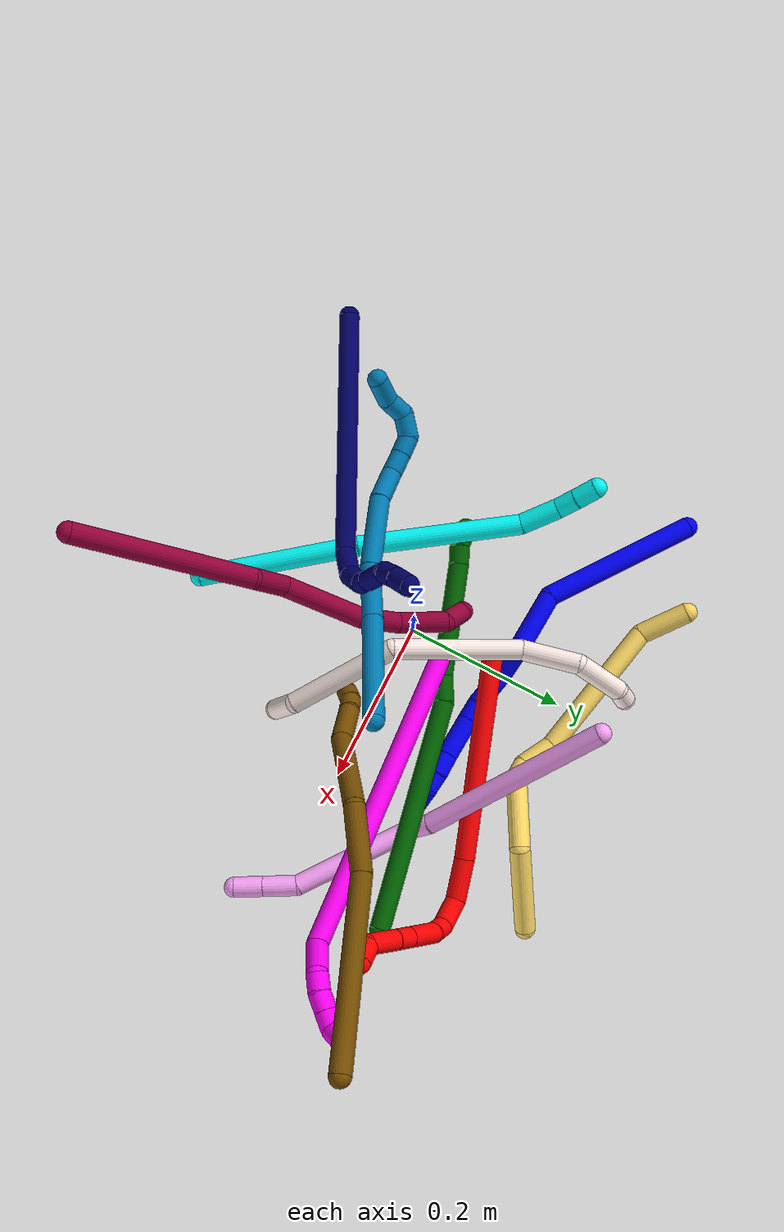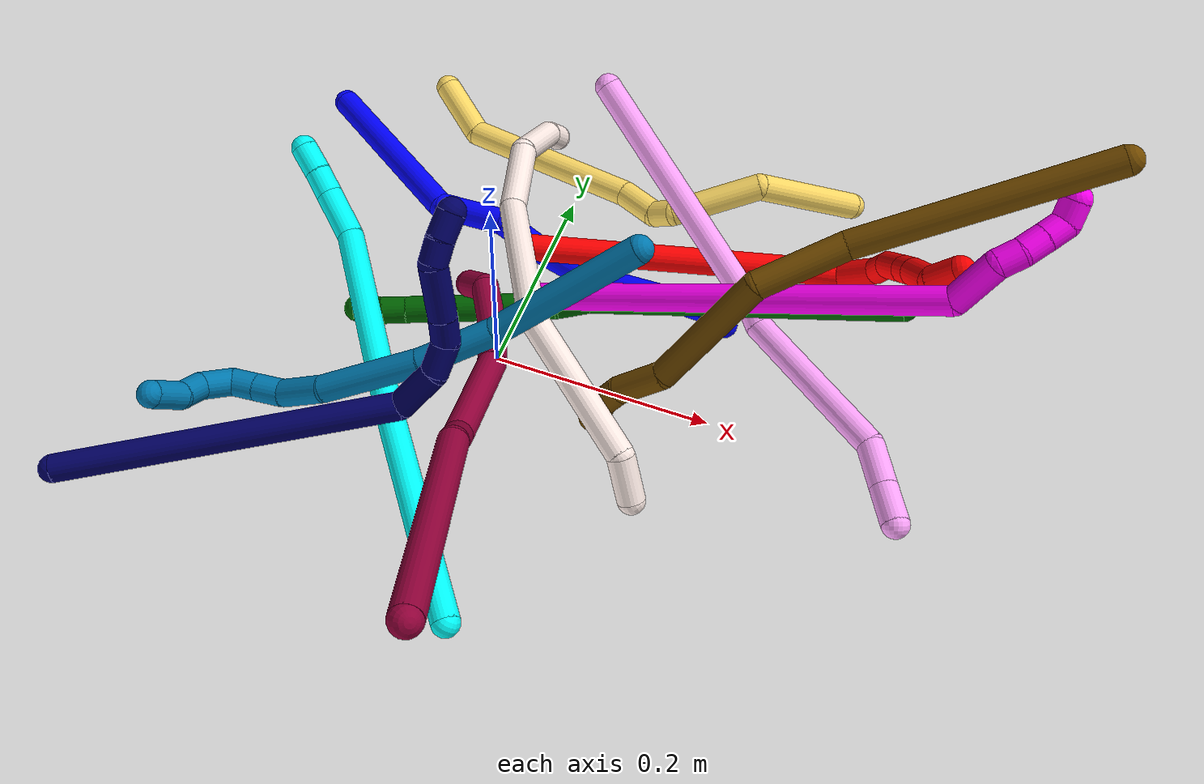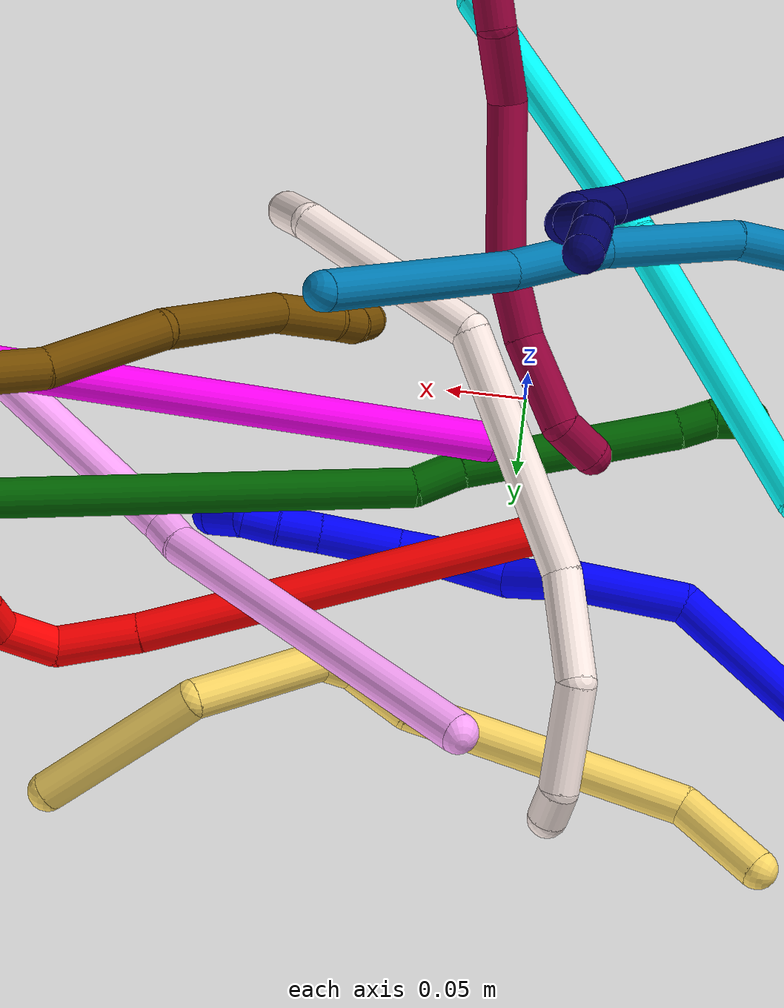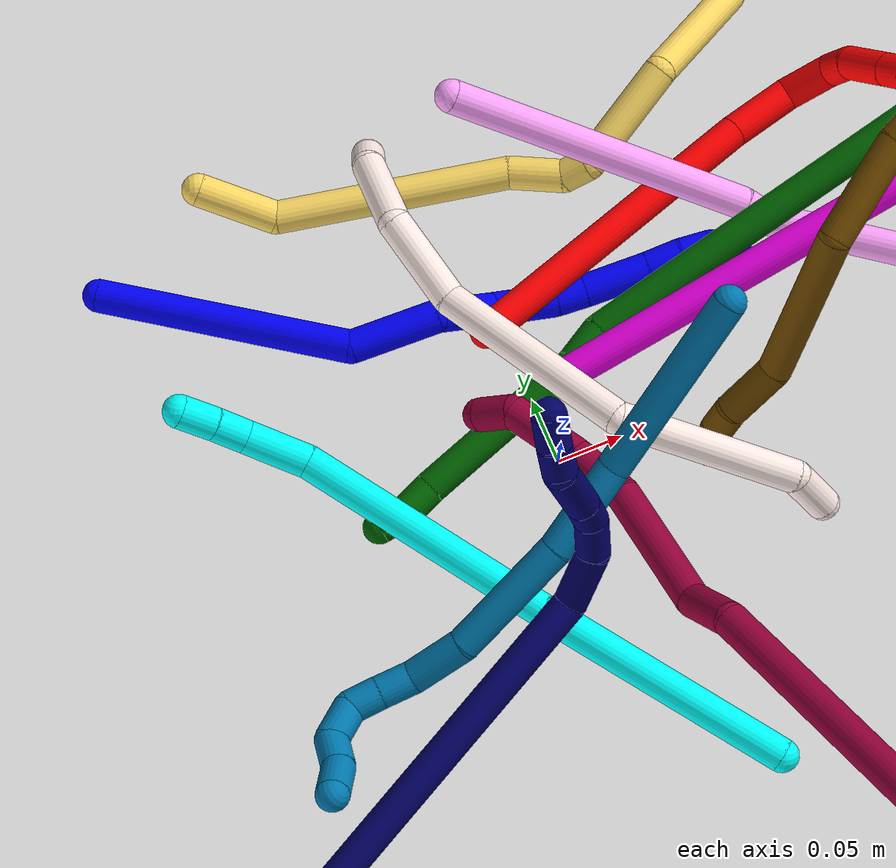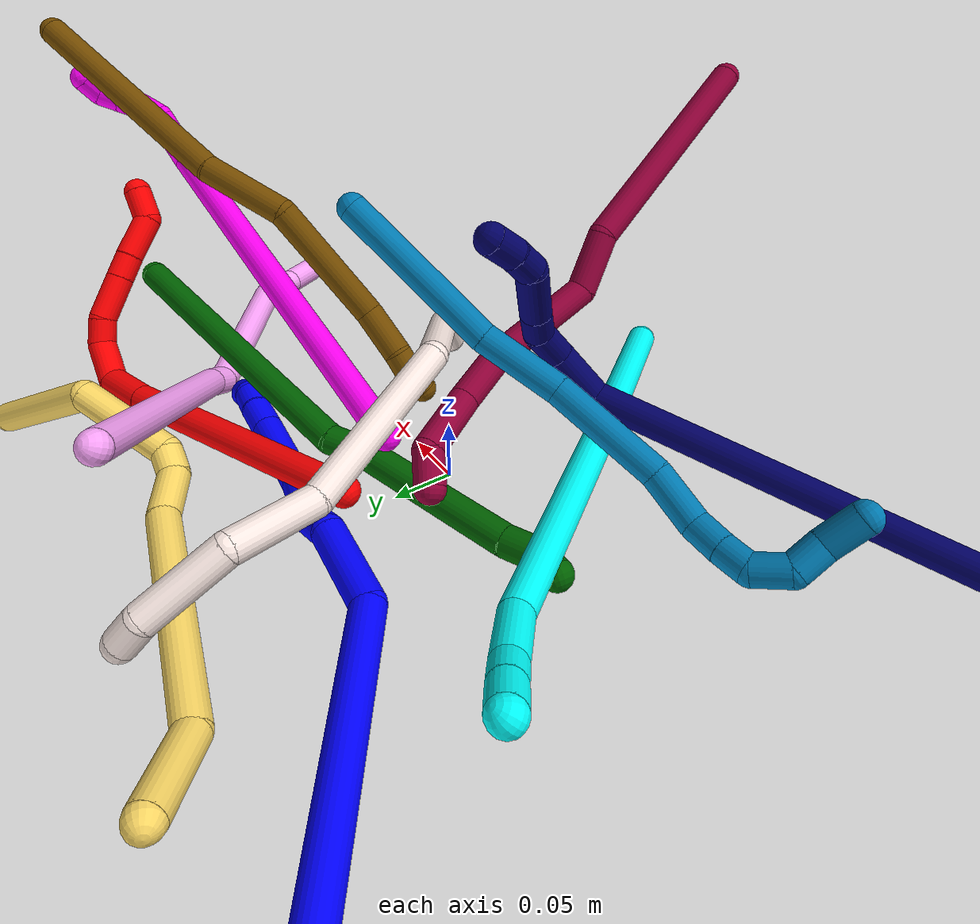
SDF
<sdf version="1.7">
 <world name="default">
  <plugin name="TubeGeneratorPlugin" filename="libtube_generator_plugin.so"/>
  <model name="photoneo_s_sensor">
   <static>1</static>
   <pose>0 0 2 1.57079 1.57079 3.14159</pose>
   <link name="link">
    <inertial><mass>0.1</mass></inertial>
    <sensor name="sensor" type="depth">
     <update_rate>30</update_rate>
     <camera>
      <horizontal_fov>1.22</horizontal_fov>
      <image><width>1920</width><height>1200</height><format>B8G8R8</format></image>
      <clip><near>0.1</near><far>4</far></clip>
      <depth_camera><output>points</output></depth_camera>
     </camera>
     <plugin name="camera_plugin" filename="libgazebo_ros_depth_camera.so">
      <baseline>0.2</baseline>
      <alwaysOn>1</alwaysOn>
      <updateRate>0.0</updateRate>
      <cameraName>camera_ir</cameraName>
      <imageTopicName>/camera/color/image_raw</imageTopicName>
      <cameraInfoTopicName>/camera/color/camera_info</cameraInfoTopicName>
      <depthImageTopicName>/camera/depth/image_raw</depthImageTopicName>
      <depthImageCameraInfoTopicName>/camera/depth/camera_info</depthImageCameraInfoTopicName>
      <pointCloudTopicName>/camera/depth/points</pointCloudTopicName>
      <frameName>fr_optical</frameName>
      <pointCloudCutoff>0.1</pointCloudCutoff>
      <pointCloudCutoffMax>2.0</pointCloudCutoffMax>
      <distortionK1>0</distortionK1>
      <distortionK2>0</distortionK2>
      <distortionK3>0</distortionK3>
      <distortionT1>0</distortionT1>
      <distortionT2>0</distortionT2>
      <CxPrime>0</CxPrime>
      <Cx>0</Cx>
      <Cy>0</Cy>
      <focalLength>0</focalLength>
      <hackBaseline>0</hackBaseline>
     </plugin>
    </sensor>
   </link>
  </model>
  <gravity>0 0 -9.8</gravity>
  <magnetic_field>6e-06 2.3e-05 -4.2e-05</magnetic_field>
  <atmosphere type="adiabatic"/>
  <physics name="default_physics" default="0" type="ode">
   <max_step_size>0.003</max_step_size>
   <real_time_factor>1</real_time_factor>
   <real_time_update_rate>1000</real_time_update_rate>
   <max_contacts>10000</max_contacts>
   <ode>
    <solver>
     <type>quick</type>
     <iters>100</iters>
     <sor>1.3</sor>
     <use_dynamic_moi_rescaling>0</use_dynamic_moi_rescaling>
    </solver>
    <constraints>
     <contact_max_correcting_vel>0</contact_max_correcting_vel>
     <contact_surface_layer>0.001</contact_surface_layer>
     <cfm>0</cfm>
     <erp>0.2</erp>
    </constraints>
   </ode>
  </physics>
  <scene><ambient>0.4 0.4 0.4 1</ambient><background>0.7 0.7 0.7 1</background><shadows>0</shadows></scene>
  <audio><device>default</device></audio>
  <spherical_coordinates>
   <surface_model>EARTH_WGS84</surface_model>
   <latitude_deg>0</latitude_deg>
   <longitude_deg>0</longitude_deg>
   <elevation>0</elevation>
   <heading_deg>0</heading_deg>
  </spherical_coordinates>
  <model name="bin">
   <static>1</static>
   <link name="bottom">
    <collision name="collision-bottom">
     <pose>0 0 -0.01 0 -0 0</pose>
     <geometry><box><size>0.8 0.6 0.02</size></box></geometry>
     <surface>
      <friction><ode><mu>100</mu><mu2>100</mu2></ode></friction>
      <contact><collide_bitmask>65535</collide_bitmask></contact>
     </surface>
    </collision>
   </link>
   <link name="west_wall">
    <collision name="collision-west_wall">
     <pose>-0.41 0 0.1 0 -0 0</pose>
     <geometry><box><size>0.02 0.6 0.2</size></box></geometry>
     <surface>
      <friction><ode><mu>100</mu><mu2>100</mu2></ode></friction>
      <contact><collide_bitmask>65535</collide_bitmask></contact>
     </surface>
    </collision>
   </link>
   <link name="east_wall">
    <collision name="collision-east_wall">
     <pose>0.41 0 0.1 0 -0 0</pose>
     <geometry><box><size>0.02 0.6 0.2</size></box></geometry>
     <surface>
      <friction><ode><mu>100</mu><mu2>100</mu2></ode></friction>
      <contact><collide_bitmask>65535</collide_bitmask></contact>
     </surface>
    </collision>
   </link>
   <link name="south_wall">
    <collision name="collision-south_wall">
     <pose>0 -0.31 0.1 0 -0 0</pose>
     <geometry><box><size>0.8 0.02 0.2</size></box></geometry>
     <surface>
      <friction><ode><mu>100</mu><mu2>100</mu2></ode></friction>
      <contact><collide_bitmask>65535</collide_bitmask></contact>
     </surface>
    </collision>
   </link>
   <link name="north_wall">
    <collision name="collision-north_wall">
     <pose>0 0.31 0.1 0 -0 0</pose>
     <geometry><box><size>0.8 0.02 0.2</size></box></geometry>
     <surface>
      <friction><ode><mu>100</mu><mu2>100</mu2></ode></friction>
      <contact><collide_bitmask>65535</collide_bitmask></contact>
     </surface>
    </collision>
   </link>
  </model>
  <model name="1">
   <static>0</static>
   <link name="1">
    <collision name="collision-cylinder-e_1_1_4">
     <pose>0.086271 0.005721 -0.043493 -3.0108 1.10039 -2.92885</pose>
     <geometry><cylinder><radius>0.0125</radius><length>0.193567</length></cylinder></geometry>
     <surface>
      <friction><ode><mu>1.16</mu><mu2>1.16</mu2><slip1>0</slip1><slip2>0</slip2></ode></friction>
      <contact><ode><kp>1e+06</kp><kd>1</kd><max_vel>0</max_vel><min_depth>0.001</min_depth></ode></contact>
     </surface>
    </collision>
    <visual name="visual-cylinder-e_1_1_4">
     <pose>0.086271 0.005721 -0.043493 -3.0108 1.10039 -2.92885</pose>
     <geometry><cylinder><radius>0.0125</radius><length>0.193567</length></cylinder></geometry>
     <material><ambient>0 0 1 1</ambient></material>
    </visual>
    <collision name="collision-cylinder-e_2_4_5">
     <pose>0.205229 0.003794 -0.08635 1.48794 1.34016 1.26025</pose>
     <geometry><cylinder><radius>0.0125</radius><length>0.067152</length></cylinder></geometry>
     <surface>
      <friction><ode><mu>1.16</mu><mu2>1.16</mu2><slip1>0</slip1><slip2>0</slip2></ode></friction>
      <contact><ode><kp>1e+06</kp><kd>1</kd><max_vel>0</max_vel><min_depth>0.001</min_depth></ode></contact>
     </surface>
    </collision>
    <visual name="visual-cylinder-e_2_4_5">
     <pose>0.205229 0.003794 -0.08635 1.48794 1.34016 1.26025</pose>
     <geometry><cylinder><radius>0.0125</radius><length>0.067152</length></cylinder></geometry>
     <material><ambient>0 0 1 1</ambient></material>
    </visual>
    <collision name="collision-cylinder-e_3_5_6">
     <pose>0.259807 0.003205 -0.079294 -0.832785 1.15969 -0.56387</pose>
     <geometry><cylinder><radius>0.0125</radius><length>0.047761</length></cylinder></geometry>
     <surface>
      <friction><ode><mu>1.16</mu><mu2>1.16</mu2><slip1>0</slip1><slip2>0</slip2></ode></friction>
      <contact><ode><kp>1e+06</kp><kd>1</kd><max_vel>0</max_vel><min_depth>0.001</min_depth></ode></contact>
     </surface>
    </collision>
    <visual name="visual-cylinder-e_3_5_6">
     <pose>0.259807 0.003205 -0.079294 -0.832785 1.15969 -0.56387</pose>
     <geometry><cylinder><radius>0.0125</radius><length>0.047761</length></cylinder></geometry>
     <material><ambient>0 0 1 1</ambient></material>
    </visual>
    <collision name="collision-cylinder-e_4_6_7">
     <pose>0.305501 0.010683 -0.07315 -2.15731 1.54974 -2.13966</pose>
     <geometry><cylinder><radius>0.0125</radius><length>0.047616</length></cylinder></geometry>
     <surface>
      <friction><ode><mu>1.16</mu><mu2>1.16</mu2><slip1>0</slip1><slip2>0</slip2></ode></friction>
      <contact><ode><kp>1e+06</kp><kd>1</kd><max_vel>0</max_vel><min_depth>0.001</min_depth></ode></contact>
     </surface>
    </collision>
    <visual name="visual-cylinder-e_4_6_7">
     <pose>0.305501 0.010683 -0.07315 -2.15731 1.54974 -2.13966</pose>
     <geometry><cylinder><radius>0.0125</radius><length>0.047616</length></cylinder></geometry>
     <material><ambient>0 0 1 1</ambient></material>
    </visual>
    <collision name="collision-cylinder-e_5_7_8">
     <pose>0.3406 0.009294 -0.072971 1.32283 1.40736 1.16748</pose>
     <geometry><cylinder><radius>0.0125</radius><length>0.022898</length></cylinder></geometry>
     <surface>
      <friction><ode><mu>1.16</mu><mu2>1.16</mu2><slip1>0</slip1><slip2>0</slip2></ode></friction>
      <contact><ode><kp>1e+06</kp><kd>1</kd><max_vel>0</max_vel><min_depth>0.001</min_depth></ode></contact>
     </surface>
    </collision>
    <visual name="visual-cylinder-e_5_7_8">
     <pose>0.3406 0.009294 -0.072971 1.32283 1.40736 1.16748</pose>
     <geometry><cylinder><radius>0.0125</radius><length>0.022898</length></cylinder></geometry>
     <material><ambient>0 0 1 1</ambient></material>
    </visual>
    <collision name="collision-cylinder-e_6_8_9">
     <pose>0.376205 0.001886 -0.07195 1.47064 1.34319 1.2467</pose>
     <geometry><cylinder><radius>0.0125</radius><length>0.049904</length></cylinder></geometry>
     <surface>
      <friction><ode><mu>1.16</mu><mu2>1.16</mu2><slip1>0</slip1><slip2>0</slip2></ode></friction>
      <contact><ode><kp>1e+06</kp><kd>1</kd><max_vel>0</max_vel><min_depth>0.001</min_depth></ode></contact>
     </surface>
    </collision>
    <visual name="visual-cylinder-e_6_8_9">
     <pose>0.376205 0.001886 -0.07195 1.47064 1.34319 1.2467</pose>
     <geometry><cylinder><radius>0.0125</radius><length>0.049904</length></cylinder></geometry>
     <material><ambient>0 0 1 1</ambient></material>
    </visual>
    <collision name="collision-cylinder-e_7_9_10">
     <pose>0.413148 -0.007413 -0.07106 1.48252 1.28509 1.20143</pose>
     <geometry><cylinder><radius>0.0125</radius><length>0.026336</length></cylinder></geometry>
     <surface>
      <friction><ode><mu>1.16</mu><mu2>1.16</mu2><slip1>0</slip1><slip2>0</slip2></ode></friction>
      <contact><ode><kp>1e+06</kp><kd>1</kd><max_vel>0</max_vel><min_depth>0.001</min_depth></ode></contact>
     </surface>
    </collision>
    <visual name="visual-cylinder-e_7_9_10">
     <pose>0.413148 -0.007413 -0.07106 1.48252 1.28509 1.20143</pose>
     <geometry><cylinder><radius>0.0125</radius><length>0.026336</length></cylinder></geometry>
     <material><ambient>0 0 1 1</ambient></material>
    </visual>
    <collision name="collision-cylinder-e_8_10_11">
     <pose>0.436399 -0.012842 -0.070745 1.57785 1.40908 1.41604</pose>
     <geometry><cylinder><radius>0.0125</radius><length>0.021515</length></cylinder></geometry>
     <surface>
      <friction><ode><mu>1.16</mu><mu2>1.16</mu2><slip1>0</slip1><slip2>0</slip2></ode></friction>
      <contact><ode><kp>1e+06</kp><kd>1</kd><max_vel>0</max_vel><min_depth>0.001</min_depth></ode></contact>
     </surface>
    </collision>
    <visual name="visual-cylinder-e_8_10_11">
     <pose>0.436399 -0.012842 -0.070745 1.57785 1.40908 1.41604</pose>
     <geometry><cylinder><radius>0.0125</radius><length>0.021515</length></cylinder></geometry>
     <material><ambient>0 0 1 1</ambient></material>
    </visual>
    <collision name="collision-cylinder-e_9_11_2">
     <pose>0.457691 -0.010892 -0.067992 -0.92659 1.16351 -0.634878</pose>
     <geometry><cylinder><radius>0.0125</radius><length>0.02325</length></cylinder></geometry>
     <surface>
      <friction><ode><mu>1.16</mu><mu2>1.16</mu2><slip1>0</slip1><slip2>0</slip2></ode></friction>
      <contact><ode><kp>1e+06</kp><kd>1</kd><max_vel>0</max_vel><min_depth>0.001</min_depth></ode></contact>
     </surface>
    </collision>
    <visual name="visual-cylinder-e_9_11_2">
     <pose>0.457691 -0.010892 -0.067992 -0.92659 1.16351 -0.634878</pose>
     <geometry><cylinder><radius>0.0125</radius><length>0.02325</length></cylinder></geometry>
     <material><ambient>0 0 1 1</ambient></material>
    </visual>
    <collision name="collision-sphere-2">
     <pose>0.468364 -0.00721 -0.065227 0 -0 0</pose>
     <geometry><sphere><radius>0.0125</radius></sphere></geometry>
     <surface>
      <friction><ode><mu>1.16</mu><mu2>1.16</mu2><slip1>0</slip1><slip2>0</slip2></ode></friction>
      <contact><ode><kp>1e+06</kp><kd>1</kd><max_vel>0</max_vel><min_depth>0.001</min_depth></ode></contact>
     </surface>
    </collision>
    <visual name="visual-sphere-2">
     <pose>0.468364 -0.00721 -0.065227 0 -0 0</pose>
     <geometry><sphere><radius>0.0125</radius></sphere></geometry>
     <material><ambient>0 0 1 1</ambient></material>
    </visual>
    <collision name="collision-sphere-11">
     <pose>0.447017 -0.014574 -0.070758 0 -0 0</pose>
     <geometry><sphere><radius>0.0125</radius></sphere></geometry>
     <surface>
      <friction><ode><mu>1.16</mu><mu2>1.16</mu2><slip1>0</slip1><slip2>0</slip2></ode></friction>
      <contact><ode><kp>1e+06</kp><kd>1</kd><max_vel>0</max_vel><min_depth>0.001</min_depth></ode></contact>
     </surface>
    </collision>
    <visual name="visual-sphere-11">
     <pose>0.447017 -0.014574 -0.070758 0 -0 0</pose>
     <geometry><sphere><radius>0.0125</radius></sphere></geometry>
     <material><ambient>0 0 1 1</ambient></material>
    </visual>
    <collision name="collision-sphere-10">
     <pose>0.425782 -0.01111 -0.070733 0 -0 0</pose>
     <geometry><sphere><radius>0.0125</radius></sphere></geometry>
     <surface>
      <friction><ode><mu>1.16</mu><mu2>1.16</mu2><slip1>0</slip1><slip2>0</slip2></ode></friction>
      <contact><ode><kp>1e+06</kp><kd>1</kd><max_vel>0</max_vel><min_depth>0.001</min_depth></ode></contact>
     </surface>
    </collision>
    <visual name="visual-sphere-10">
     <pose>0.425782 -0.01111 -0.070733 0 -0 0</pose>
     <geometry><sphere><radius>0.0125</radius></sphere></geometry>
     <material><ambient>0 0 1 1</ambient></material>
    </visual>
    <collision name="collision-sphere-9">
     <pose>0.400514 -0.003716 -0.071387 0 -0 0</pose>
     <geometry><sphere><radius>0.0125</radius></sphere></geometry>
     <surface>
      <friction><ode><mu>1.16</mu><mu2>1.16</mu2><slip1>0</slip1><slip2>0</slip2></ode></friction>
      <contact><ode><kp>1e+06</kp><kd>1</kd><max_vel>0</max_vel><min_depth>0.001</min_depth></ode></contact>
     </surface>
    </collision>
    <visual name="visual-sphere-9">
     <pose>0.400514 -0.003716 -0.071387 0 -0 0</pose>
     <geometry><sphere><radius>0.0125</radius></sphere></geometry>
     <material><ambient>0 0 1 1</ambient></material>
    </visual>
    <collision name="collision-sphere-4">
     <pose>0.172542 0.011443 -0.086985 0 -0 0</pose>
     <geometry><sphere><radius>0.0125</radius></sphere></geometry>
     <surface>
      <friction><ode><mu>1.16</mu><mu2>1.16</mu2><slip1>0</slip1><slip2>0</slip2></ode></friction>
      <contact><ode><kp>1e+06</kp><kd>1</kd><max_vel>0</max_vel><min_depth>0.001</min_depth></ode></contact>
     </surface>
    </collision>
    <visual name="visual-sphere-4">
     <pose>0.172542 0.011443 -0.086985 0 -0 0</pose>
     <geometry><sphere><radius>0.0125</radius></sphere></geometry>
     <material><ambient>0 0 1 1</ambient></material>
    </visual>
    <collision name="collision-sphere-1">
     <geometry><sphere><radius>0.0125</radius></sphere></geometry>
     <surface>
      <friction><ode><mu>1.16</mu><mu2>1.16</mu2><slip1>0</slip1><slip2>0</slip2></ode></friction>
      <contact><ode><kp>1e+06</kp><kd>1</kd><max_vel>0</max_vel><min_depth>0.001</min_depth></ode></contact>
     </surface>
    </collision>
    <visual name="visual-sphere-1">
     <geometry><sphere><radius>0.0125</radius></sphere></geometry>
     <material><ambient>0 0 1 1</ambient></material>
    </visual>
    <collision name="collision-sphere-8">
     <pose>0.351897 0.007488 -0.072513 0 -0 0</pose>
     <geometry><sphere><radius>0.0125</radius></sphere></geometry>
     <surface>
      <friction><ode><mu>1.16</mu><mu2>1.16</mu2><slip1>0</slip1><slip2>0</slip2></ode></friction>
      <contact><ode><kp>1e+06</kp><kd>1</kd><max_vel>0</max_vel><min_depth>0.001</min_depth></ode></contact>
     </surface>
    </collision>
    <visual name="visual-sphere-8">
     <pose>0.351897 0.007488 -0.072513 0 -0 0</pose>
     <geometry><sphere><radius>0.0125</radius></sphere></geometry>
     <material><ambient>0 0 1 1</ambient></material>
    </visual>
    <collision name="collision-sphere-5">
     <pose>0.237916 -0.003855 -0.085715 0 -0 0</pose>
     <geometry><sphere><radius>0.0125</radius></sphere></geometry>
     <surface>
      <friction><ode><mu>1.16</mu><mu2>1.16</mu2><slip1>0</slip1><slip2>0</slip2></ode></friction>
      <contact><ode><kp>1e+06</kp><kd>1</kd><max_vel>0</max_vel><min_depth>0.001</min_depth></ode></contact>
     </surface>
    </collision>
    <visual name="visual-sphere-5">
     <pose>0.237916 -0.003855 -0.085715 0 -0 0</pose>
     <geometry><sphere><radius>0.0125</radius></sphere></geometry>
     <material><ambient>0 0 1 1</ambient></material>
    </visual>
    <collision name="collision-sphere-6">
     <pose>0.281698 0.010265 -0.072873 0 -0 0</pose>
     <geometry><sphere><radius>0.0125</radius></sphere></geometry>
     <surface>
      <friction><ode><mu>1.16</mu><mu2>1.16</mu2><slip1>0</slip1><slip2>0</slip2></ode></friction>
      <contact><ode><kp>1e+06</kp><kd>1</kd><max_vel>0</max_vel><min_depth>0.001</min_depth></ode></contact>
     </surface>
    </collision>
    <visual name="visual-sphere-6">
     <pose>0.281698 0.010265 -0.072873 0 -0 0</pose>
     <geometry><sphere><radius>0.0125</radius></sphere></geometry>
     <material><ambient>0 0 1 1</ambient></material>
    </visual>
    <collision name="collision-sphere-7">
     <pose>0.329303 0.0111 -0.073428 0 -0 0</pose>
     <geometry><sphere><radius>0.0125</radius></sphere></geometry>
     <surface>
      <friction><ode><mu>1.16</mu><mu2>1.16</mu2><slip1>0</slip1><slip2>0</slip2></ode></friction>
      <contact><ode><kp>1e+06</kp><kd>1</kd><max_vel>0</max_vel><min_depth>0.001</min_depth></ode></contact>
     </surface>
    </collision>
    <visual name="visual-sphere-7">
     <pose>0.329303 0.0111 -0.073428 0 -0 0</pose>
     <geometry><sphere><radius>0.0125</radius></sphere></geometry>
     <material><ambient>0 0 1 1</ambient></material>
    </visual>
    <inertial>
     <pose>0.229841 0.003212 -0.063447 0 -0 0</pose>
     <mass>0.5</mass>
     <inertia>
      <ixx>-0.000279</ixx>
      <ixy>0</ixy>
      <ixz>0</ixz>
      <iyy>0.000623</iyy>
      <iyz>0</iyz>
      <izz>-0.000648</izz>
     </inertia>
    </inertial>
   </link>
   <pose>-0.267585 0.241477 0.013085 -2.08336 0.084647 -0.186113</pose>
  </model>
  <model name="2">
   <static>0</static>
   <link name="2">
    <collision name="collision-cylinder-e_1_1_4">
     <pose>0.054933 0.042106 0.104432 -0.38325 0.453889 -0.089541</pose>
     <geometry><cylinder><radius>0.0125</radius><length>0.250572</length></cylinder></geometry>
     <surface>
      <friction><ode><mu>1.16</mu><mu2>1.16</mu2><slip1>0</slip1><slip2>0</slip2></ode></friction>
      <contact><ode><kp>1e+06</kp><kd>1</kd><max_vel>0</max_vel><min_depth>0.001</min_depth></ode></contact>
     </surface>
    </collision>
    <visual name="visual-cylinder-e_1_1_4">
     <pose>0.054933 0.042106 0.104432 -0.38325 0.453889 -0.089541</pose>
     <geometry><cylinder><radius>0.0125</radius><length>0.250572</length></cylinder></geometry>
     <material><ambient>1 0 0 1</ambient></material>
    </visual>
    <collision name="collision-cylinder-e_2_4_5">
     <pose>0.121935 0.091105 0.23143 -0.296483 0.472783 -0.071918</pose>
     <geometry><cylinder><radius>0.0125</radius><length>0.053005</length></cylinder></geometry>
     <surface>
      <friction><ode><mu>1.16</mu><mu2>1.16</mu2><slip1>0</slip1><slip2>0</slip2></ode></friction>
      <contact><ode><kp>1e+06</kp><kd>1</kd><max_vel>0</max_vel><min_depth>0.001</min_depth></ode></contact>
     </surface>
    </collision>
    <visual name="visual-cylinder-e_2_4_5">
     <pose>0.121935 0.091105 0.23143 -0.296483 0.472783 -0.071918</pose>
     <geometry><cylinder><radius>0.0125</radius><length>0.053005</length></cylinder></geometry>
     <material><ambient>1 0 0 1</ambient></material>
    </visual>
    <collision name="collision-cylinder-e_3_5_6">
     <pose>0.134001 0.092144 0.272741 0.302701 -0.000133 -2e-05</pose>
     <geometry><cylinder><radius>0.0125</radius><length>0.039276</length></cylinder></geometry>
     <surface>
      <friction><ode><mu>1.16</mu><mu2>1.16</mu2><slip1>0</slip1><slip2>0</slip2></ode></friction>
      <contact><ode><kp>1e+06</kp><kd>1</kd><max_vel>0</max_vel><min_depth>0.001</min_depth></ode></contact>
     </surface>
    </collision>
    <visual name="visual-cylinder-e_3_5_6">
     <pose>0.134001 0.092144 0.272741 0.302701 -0.000133 -2e-05</pose>
     <geometry><cylinder><radius>0.0125</radius><length>0.039276</length></cylinder></geometry>
     <material><ambient>1 0 0 1</ambient></material>
    </visual>
    <collision name="collision-cylinder-e_4_6_7">
     <pose>0.129575 0.078464 0.299457 0.77624 -0.377038 -0.155693</pose>
     <geometry><cylinder><radius>0.0125</radius><length>0.024029</length></cylinder></geometry>
     <surface>
      <friction><ode><mu>1.16</mu><mu2>1.16</mu2><slip1>0</slip1><slip2>0</slip2></ode></friction>
      <contact><ode><kp>1e+06</kp><kd>1</kd><max_vel>0</max_vel><min_depth>0.001</min_depth></ode></contact>
     </surface>
    </collision>
    <visual name="visual-cylinder-e_4_6_7">
     <pose>0.129575 0.078464 0.299457 0.77624 -0.377038 -0.155693</pose>
     <geometry><cylinder><radius>0.0125</radius><length>0.024029</length></cylinder></geometry>
     <material><ambient>1 0 0 1</ambient></material>
    </visual>
    <collision name="collision-cylinder-e_5_7_8">
     <pose>0.122263 0.052913 0.317471 1.05527 -0.140842 -0.082164</pose>
     <geometry><cylinder><radius>0.0125</radius><length>0.041152</length></cylinder></geometry>
     <surface>
      <friction><ode><mu>1.16</mu><mu2>1.16</mu2><slip1>0</slip1><slip2>0</slip2></ode></friction>
      <contact><ode><kp>1e+06</kp><kd>1</kd><max_vel>0</max_vel><min_depth>0.001</min_depth></ode></contact>
     </surface>
    </collision>
    <visual name="visual-cylinder-e_5_7_8">
     <pose>0.122263 0.052913 0.317471 1.05527 -0.140842 -0.082164</pose>
     <geometry><cylinder><radius>0.0125</radius><length>0.041152</length></cylinder></geometry>
     <material><ambient>1 0 0 1</ambient></material>
    </visual>
    <collision name="collision-cylinder-e_6_8_9">
     <pose>0.117909 0.025554 0.33297 1.05555 -0.131649 -0.076816</pose>
     <geometry><cylinder><radius>0.0125</radius><length>0.022337</length></cylinder></geometry>
     <surface>
      <friction><ode><mu>1.16</mu><mu2>1.16</mu2><slip1>0</slip1><slip2>0</slip2></ode></friction>
      <contact><ode><kp>1e+06</kp><kd>1</kd><max_vel>0</max_vel><min_depth>0.001</min_depth></ode></contact>
     </surface>
    </collision>
    <visual name="visual-cylinder-e_6_8_9">
     <pose>0.117909 0.025554 0.33297 1.05555 -0.131649 -0.076816</pose>
     <geometry><cylinder><radius>0.0125</radius><length>0.022337</length></cylinder></geometry>
     <material><ambient>1 0 0 1</ambient></material>
    </visual>
    <collision name="collision-cylinder-e_7_9_10">
     <pose>0.115233 -0.001687 0.347939 1.07544 -0.060384 -0.036016</pose>
     <geometry><cylinder><radius>0.0125</radius><length>0.040099</length></cylinder></geometry>
     <surface>
      <friction><ode><mu>1.16</mu><mu2>1.16</mu2><slip1>0</slip1><slip2>0</slip2></ode></friction>
      <contact><ode><kp>1e+06</kp><kd>1</kd><max_vel>0</max_vel><min_depth>0.001</min_depth></ode></contact>
     </surface>
    </collision>
    <visual name="visual-cylinder-e_7_9_10">
     <pose>0.115233 -0.001687 0.347939 1.07544 -0.060384 -0.036016</pose>
     <geometry><cylinder><radius>0.0125</radius><length>0.040099</length></cylinder></geometry>
     <material><ambient>1 0 0 1</ambient></material>
    </visual>
    <collision name="collision-cylinder-e_8_10_2">
     <pose>0.110493 -0.024093 0.370962 0.341258 -0.241392 -0.04179</pose>
     <geometry><cylinder><radius>0.0125</radius><length>0.02953</length></cylinder></geometry>
     <surface>
      <friction><ode><mu>1.16</mu><mu2>1.16</mu2><slip1>0</slip1><slip2>0</slip2></ode></friction>
      <contact><ode><kp>1e+06</kp><kd>1</kd><max_vel>0</max_vel><min_depth>0.001</min_depth></ode></contact>
     </surface>
    </collision>
    <visual name="visual-cylinder-e_8_10_2">
     <pose>0.110493 -0.024093 0.370962 0.341258 -0.241392 -0.04179</pose>
     <geometry><cylinder><radius>0.0125</radius><length>0.02953</length></cylinder></geometry>
     <material><ambient>1 0 0 1</ambient></material>
    </visual>
    <collision name="collision-sphere-2">
     <pose>0.106963 -0.028891 0.384472 0 -0 0</pose>
     <geometry><sphere><radius>0.0125</radius></sphere></geometry>
     <surface>
      <friction><ode><mu>1.16</mu><mu2>1.16</mu2><slip1>0</slip1><slip2>0</slip2></ode></friction>
      <contact><ode><kp>1e+06</kp><kd>1</kd><max_vel>0</max_vel><min_depth>0.001</min_depth></ode></contact>
     </surface>
    </collision>
    <visual name="visual-sphere-2">
     <pose>0.106963 -0.028891 0.384472 0 -0 0</pose>
     <geometry><sphere><radius>0.0125</radius></sphere></geometry>
     <material><ambient>1 0 0 1</ambient></material>
    </visual>
    <collision name="collision-sphere-10">
     <pose>0.114023 -0.019295 0.357452 0 -0 0</pose>
     <geometry><sphere><radius>0.0125</radius></sphere></geometry>
     <surface>
      <friction><ode><mu>1.16</mu><mu2>1.16</mu2><slip1>0</slip1><slip2>0</slip2></ode></friction>
      <contact><ode><kp>1e+06</kp><kd>1</kd><max_vel>0</max_vel><min_depth>0.001</min_depth></ode></contact>
     </surface>
    </collision>
    <visual name="visual-sphere-10">
     <pose>0.114023 -0.019295 0.357452 0 -0 0</pose>
     <geometry><sphere><radius>0.0125</radius></sphere></geometry>
     <material><ambient>1 0 0 1</ambient></material>
    </visual>
    <collision name="collision-sphere-9">
     <pose>0.116443 0.01592 0.338426 0 -0 0</pose>
     <geometry><sphere><radius>0.0125</radius></sphere></geometry>
     <surface>
      <friction><ode><mu>1.16</mu><mu2>1.16</mu2><slip1>0</slip1><slip2>0</slip2></ode></friction>
      <contact><ode><kp>1e+06</kp><kd>1</kd><max_vel>0</max_vel><min_depth>0.001</min_depth></ode></contact>
     </surface>
    </collision>
    <visual name="visual-sphere-9">
     <pose>0.116443 0.01592 0.338426 0 -0 0</pose>
     <geometry><sphere><radius>0.0125</radius></sphere></geometry>
     <material><ambient>1 0 0 1</ambient></material>
    </visual>
    <collision name="collision-sphere-4">
     <pose>0.109867 0.084211 0.208864 0 -0 0</pose>
     <geometry><sphere><radius>0.0125</radius></sphere></geometry>
     <surface>
      <friction><ode><mu>1.16</mu><mu2>1.16</mu2><slip1>0</slip1><slip2>0</slip2></ode></friction>
      <contact><ode><kp>1e+06</kp><kd>1</kd><max_vel>0</max_vel><min_depth>0.001</min_depth></ode></contact>
     </surface>
    </collision>
    <visual name="visual-sphere-4">
     <pose>0.109867 0.084211 0.208864 0 -0 0</pose>
     <geometry><sphere><radius>0.0125</radius></sphere></geometry>
     <material><ambient>1 0 0 1</ambient></material>
    </visual>
    <collision name="collision-sphere-1">
     <geometry><sphere><radius>0.0125</radius></sphere></geometry>
     <surface>
      <friction><ode><mu>1.16</mu><mu2>1.16</mu2><slip1>0</slip1><slip2>0</slip2></ode></friction>
      <contact><ode><kp>1e+06</kp><kd>1</kd><max_vel>0</max_vel><min_depth>0.001</min_depth></ode></contact>
     </surface>
    </collision>
    <visual name="visual-sphere-1">
     <geometry><sphere><radius>0.0125</radius></sphere></geometry>
     <material><ambient>1 0 0 1</ambient></material>
    </visual>
    <collision name="collision-sphere-8">
     <pose>0.119375 0.035189 0.327515 0 -0 0</pose>
     <geometry><sphere><radius>0.0125</radius></sphere></geometry>
     <surface>
      <friction><ode><mu>1.16</mu><mu2>1.16</mu2><slip1>0</slip1><slip2>0</slip2></ode></friction>
      <contact><ode><kp>1e+06</kp><kd>1</kd><max_vel>0</max_vel><min_depth>0.001</min_depth></ode></contact>
     </surface>
    </collision>
    <visual name="visual-sphere-8">
     <pose>0.119375 0.035189 0.327515 0 -0 0</pose>
     <geometry><sphere><radius>0.0125</radius></sphere></geometry>
     <material><ambient>1 0 0 1</ambient></material>
    </visual>
    <collision name="collision-sphere-5">
     <pose>0.134003 0.097998 0.253996 0 -0 0</pose>
     <geometry><sphere><radius>0.0125</radius></sphere></geometry>
     <surface>
      <friction><ode><mu>1.16</mu><mu2>1.16</mu2><slip1>0</slip1><slip2>0</slip2></ode></friction>
      <contact><ode><kp>1e+06</kp><kd>1</kd><max_vel>0</max_vel><min_depth>0.001</min_depth></ode></contact>
     </surface>
    </collision>
    <visual name="visual-sphere-5">
     <pose>0.134003 0.097998 0.253996 0 -0 0</pose>
     <geometry><sphere><radius>0.0125</radius></sphere></geometry>
     <material><ambient>1 0 0 1</ambient></material>
    </visual>
    <collision name="collision-sphere-6">
     <pose>0.133998 0.08629 0.291486 0 -0 0</pose>
     <geometry><sphere><radius>0.0125</radius></sphere></geometry>
     <surface>
      <friction><ode><mu>1.16</mu><mu2>1.16</mu2><slip1>0</slip1><slip2>0</slip2></ode></friction>
      <contact><ode><kp>1e+06</kp><kd>1</kd><max_vel>0</max_vel><min_depth>0.001</min_depth></ode></contact>
     </surface>
    </collision>
    <visual name="visual-sphere-6">
     <pose>0.133998 0.08629 0.291486 0 -0 0</pose>
     <geometry><sphere><radius>0.0125</radius></sphere></geometry>
     <material><ambient>1 0 0 1</ambient></material>
    </visual>
    <collision name="collision-sphere-7">
     <pose>0.125152 0.070638 0.307428 0 -0 0</pose>
     <geometry><sphere><radius>0.0125</radius></sphere></geometry>
     <surface>
      <friction><ode><mu>1.16</mu><mu2>1.16</mu2><slip1>0</slip1><slip2>0</slip2></ode></friction>
      <contact><ode><kp>1e+06</kp><kd>1</kd><max_vel>0</max_vel><min_depth>0.001</min_depth></ode></contact>
     </surface>
    </collision>
    <visual name="visual-sphere-7">
     <pose>0.125152 0.070638 0.307428 0 -0 0</pose>
     <geometry><sphere><radius>0.0125</radius></sphere></geometry>
     <material><ambient>1 0 0 1</ambient></material>
    </visual>
    <inertial>
     <pose>0.088306 0.045706 0.203502 0 -0 0</pose>
     <mass>0.5</mass>
     <inertia>
      <ixx>0.001123</ixx>
      <ixy>0</ixy>
      <ixz>0</ixz>
      <iyy>0.001162</iyy>
      <iyz>0</iyz>
      <izz>-0.000982</izz>
     </inertia>
    </inertial>
   </link>
   <pose>-0.016527 0.099616 0.042227 -0.761967 0.88818 -0.623274</pose>
  </model>
  <model name="3">
   <static>0</static>
   <link name="3">
    <collision name="collision-cylinder-e_1_1_4">
     <pose>-0.059244 0.069343 -0.038996 -2.08308 -0.640087 1.03106</pose>
     <geometry><cylinder><radius>0.0125</radius><length>0.198383</length></cylinder></geometry>
     <surface>
      <friction><ode><mu>1.16</mu><mu2>1.16</mu2><slip1>0</slip1><slip2>0</slip2></ode></friction>
      <contact><ode><kp>1e+06</kp><kd>1</kd><max_vel>0</max_vel><min_depth>0.001</min_depth></ode></contact>
     </surface>
    </collision>
    <visual name="visual-cylinder-e_1_1_4">
     <pose>-0.059244 0.069343 -0.038996 -2.08308 -0.640087 1.03106</pose>
     <geometry><cylinder><radius>0.0125</radius><length>0.198383</length></cylinder></geometry>
     <material><ambient>0.003922 1 0.996078 1</ambient></material>
    </visual>
    <collision name="collision-cylinder-e_2_4_5">
     <pose>-0.186497 0.20314 -0.113076 -2.06928 -0.747408 1.16663</pose>
     <geometry><cylinder><radius>0.0125</radius><length>0.200106</length></cylinder></geometry>
     <surface>
      <friction><ode><mu>1.16</mu><mu2>1.16</mu2><slip1>0</slip1><slip2>0</slip2></ode></friction>
      <contact><ode><kp>1e+06</kp><kd>1</kd><max_vel>0</max_vel><min_depth>0.001</min_depth></ode></contact>
     </surface>
    </collision>
    <visual name="visual-cylinder-e_2_4_5">
     <pose>-0.186497 0.20314 -0.113076 -2.06928 -0.747408 1.16663</pose>
     <geometry><cylinder><radius>0.0125</radius><length>0.200106</length></cylinder></geometry>
     <material><ambient>0.003922 1 0.996078 1</ambient></material>
    </visual>
    <collision name="collision-cylinder-e_3_5_6">
     <pose>-0.264411 0.288225 -0.156956 -1.97377 -0.415853 0.618108</pose>
     <geometry><cylinder><radius>0.0125</radius><length>0.049034</length></cylinder></geometry>
     <surface>
      <friction><ode><mu>1.16</mu><mu2>1.16</mu2><slip1>0</slip1><slip2>0</slip2></ode></friction>
      <contact><ode><kp>1e+06</kp><kd>1</kd><max_vel>0</max_vel><min_depth>0.001</min_depth></ode></contact>
     </surface>
    </collision>
    <visual name="visual-cylinder-e_3_5_6">
     <pose>-0.264411 0.288225 -0.156956 -1.97377 -0.415853 0.618108</pose>
     <geometry><cylinder><radius>0.0125</radius><length>0.049034</length></cylinder></geometry>
     <material><ambient>0.003922 1 0.996078 1</ambient></material>
    </visual>
    <collision name="collision-cylinder-e_4_6_7">
     <pose>-0.277137 0.319765 -0.171368 -2.04631 -0.226035 0.368008</pose>
     <geometry><cylinder><radius>0.0125</radius><length>0.025181</length></cylinder></geometry>
     <surface>
      <friction><ode><mu>1.16</mu><mu2>1.16</mu2><slip1>0</slip1><slip2>0</slip2></ode></friction>
      <contact><ode><kp>1e+06</kp><kd>1</kd><max_vel>0</max_vel><min_depth>0.001</min_depth></ode></contact>
     </surface>
    </collision>
    <visual name="visual-cylinder-e_4_6_7">
     <pose>-0.277137 0.319765 -0.171368 -2.04631 -0.226035 0.368008</pose>
     <geometry><cylinder><radius>0.0125</radius><length>0.025181</length></cylinder></geometry>
     <material><ambient>0.003922 1 0.996078 1</ambient></material>
    </visual>
    <collision name="collision-cylinder-e_5_7_2">
     <pose>-0.283342 0.342732 -0.18241 -1.99357 -0.250471 0.384566</pose>
     <geometry><cylinder><radius>0.0125</radius><length>0.027297</length></cylinder></geometry>
     <surface>
      <friction><ode><mu>1.16</mu><mu2>1.16</mu2><slip1>0</slip1><slip2>0</slip2></ode></friction>
      <contact><ode><kp>1e+06</kp><kd>1</kd><max_vel>0</max_vel><min_depth>0.001</min_depth></ode></contact>
     </surface>
    </collision>
    <visual name="visual-cylinder-e_5_7_2">
     <pose>-0.283342 0.342732 -0.18241 -1.99357 -0.250471 0.384566</pose>
     <geometry><cylinder><radius>0.0125</radius><length>0.027297</length></cylinder></geometry>
     <material><ambient>0.003922 1 0.996078 1</ambient></material>
    </visual>
    <collision name="collision-sphere-2">
     <pose>-0.286724 0.35479 -0.187835 0 -0 0</pose>
     <geometry><sphere><radius>0.0125</radius></sphere></geometry>
     <surface>
      <friction><ode><mu>1.16</mu><mu2>1.16</mu2><slip1>0</slip1><slip2>0</slip2></ode></friction>
      <contact><ode><kp>1e+06</kp><kd>1</kd><max_vel>0</max_vel><min_depth>0.001</min_depth></ode></contact>
     </surface>
    </collision>
    <visual name="visual-sphere-2">
     <pose>-0.286724 0.35479 -0.187835 0 -0 0</pose>
     <geometry><sphere><radius>0.0125</radius></sphere></geometry>
     <material><ambient>0.003922 1 0.996078 1</ambient></material>
    </visual>
    <collision name="collision-sphere-7">
     <pose>-0.279959 0.330673 -0.176985 0 -0 0</pose>
     <geometry><sphere><radius>0.0125</radius></sphere></geometry>
     <surface>
      <friction><ode><mu>1.16</mu><mu2>1.16</mu2><slip1>0</slip1><slip2>0</slip2></ode></friction>
      <contact><ode><kp>1e+06</kp><kd>1</kd><max_vel>0</max_vel><min_depth>0.001</min_depth></ode></contact>
     </surface>
    </collision>
    <visual name="visual-sphere-7">
     <pose>-0.279959 0.330673 -0.176985 0 -0 0</pose>
     <geometry><sphere><radius>0.0125</radius></sphere></geometry>
     <material><ambient>0.003922 1 0.996078 1</ambient></material>
    </visual>
    <collision name="collision-sphere-6">
     <pose>-0.274315 0.308856 -0.165751 0 -0 0</pose>
     <geometry><sphere><radius>0.0125</radius></sphere></geometry>
     <surface>
      <friction><ode><mu>1.16</mu><mu2>1.16</mu2><slip1>0</slip1><slip2>0</slip2></ode></friction>
      <contact><ode><kp>1e+06</kp><kd>1</kd><max_vel>0</max_vel><min_depth>0.001</min_depth></ode></contact>
     </surface>
    </collision>
    <visual name="visual-sphere-6">
     <pose>-0.274315 0.308856 -0.165751 0 -0 0</pose>
     <geometry><sphere><radius>0.0125</radius></sphere></geometry>
     <material><ambient>0.003922 1 0.996078 1</ambient></material>
    </visual>
    <collision name="collision-sphere-5">
     <pose>-0.254507 0.267594 -0.148161 0 -0 0</pose>
     <geometry><sphere><radius>0.0125</radius></sphere></geometry>
     <surface>
      <friction><ode><mu>1.16</mu><mu2>1.16</mu2><slip1>0</slip1><slip2>0</slip2></ode></friction>
      <contact><ode><kp>1e+06</kp><kd>1</kd><max_vel>0</max_vel><min_depth>0.001</min_depth></ode></contact>
     </surface>
    </collision>
    <visual name="visual-sphere-5">
     <pose>-0.254507 0.267594 -0.148161 0 -0 0</pose>
     <geometry><sphere><radius>0.0125</radius></sphere></geometry>
     <material><ambient>0.003922 1 0.996078 1</ambient></material>
    </visual>
    <collision name="collision-sphere-1">
     <geometry><sphere><radius>0.0125</radius></sphere></geometry>
     <surface>
      <friction><ode><mu>1.16</mu><mu2>1.16</mu2><slip1>0</slip1><slip2>0</slip2></ode></friction>
      <contact><ode><kp>1e+06</kp><kd>1</kd><max_vel>0</max_vel><min_depth>0.001</min_depth></ode></contact>
     </surface>
    </collision>
    <visual name="visual-sphere-1">
     <geometry><sphere><radius>0.0125</radius></sphere></geometry>
     <material><ambient>0.003922 1 0.996078 1</ambient></material>
    </visual>
    <collision name="collision-sphere-4">
     <pose>-0.118487 0.138686 -0.077992 0 -0 0</pose>
     <geometry><sphere><radius>0.0125</radius></sphere></geometry>
     <surface>
      <friction><ode><mu>1.16</mu><mu2>1.16</mu2><slip1>0</slip1><slip2>0</slip2></ode></friction>
      <contact><ode><kp>1e+06</kp><kd>1</kd><max_vel>0</max_vel><min_depth>0.001</min_depth></ode></contact>
     </surface>
    </collision>
    <visual name="visual-sphere-4">
     <pose>-0.118487 0.138686 -0.077992 0 -0 0</pose>
     <geometry><sphere><radius>0.0125</radius></sphere></geometry>
     <material><ambient>0.003922 1 0.996078 1</ambient></material>
    </visual>
    <inertial>
     <pose>-0.1535 0.171892 -0.094708 0 -0 0</pose>
     <mass>0.5</mass>
     <inertia>
      <ixx>0.001374</ixx>
      <ixy>0</ixy>
      <ixz>0</ixz>
      <iyy>0.001313</iyy>
      <iyz>0</iyz>
      <izz>-6.6e-05</izz>
     </inertia>
    </inertial>
   </link>
   <pose>0.061919 -0.262532 0.012493 2.75175 -0.68094 -1.44195</pose>
  </model>
  <model name="4">
   <static>0</static>
   <link name="4">
    <collision name="collision-cylinder-e_1_1_4">
     <pose>0.012977 -0.065829 0.101463 0.575531 0.10689 0.031665</pose>
     <geometry><cylinder><radius>0.0125</radius><length>0.243282</length></cylinder></geometry>
     <surface>
      <friction><ode><mu>1.16</mu><mu2>1.16</mu2><slip1>0</slip1><slip2>0</slip2></ode></friction>
      <contact><ode><kp>1e+06</kp><kd>1</kd><max_vel>0</max_vel><min_depth>0.001</min_depth></ode></contact>
     </surface>
    </collision>
    <visual name="visual-cylinder-e_1_1_4">
     <pose>0.012977 -0.065829 0.101463 0.575531 0.10689 0.031665</pose>
     <geometry><cylinder><radius>0.0125</radius><length>0.243282</length></cylinder></geometry>
     <material><ambient>1 0.65098 0.996078 1</ambient></material>
    </visual>
    <collision name="collision-cylinder-e_2_4_5">
     <pose>0.027491 -0.135786 0.213614 0.368543 0.133273 0.024876</pose>
     <geometry><cylinder><radius>0.0125</radius><length>0.023121</length></cylinder></geometry>
     <surface>
      <friction><ode><mu>1.16</mu><mu2>1.16</mu2><slip1>0</slip1><slip2>0</slip2></ode></friction>
      <contact><ode><kp>1e+06</kp><kd>1</kd><max_vel>0</max_vel><min_depth>0.001</min_depth></ode></contact>
     </surface>
    </collision>
    <visual name="visual-cylinder-e_2_4_5">
     <pose>0.027491 -0.135786 0.213614 0.368543 0.133273 0.024876</pose>
     <geometry><cylinder><radius>0.0125</radius><length>0.023121</length></cylinder></geometry>
     <material><ambient>1 0.65098 0.996078 1</ambient></material>
    </visual>
    <collision name="collision-cylinder-e_3_5_6">
     <pose>0.069698 -0.183652 0.274767 0.714124 0.547026 0.208556</pose>
     <geometry><cylinder><radius>0.0125</radius><length>0.156382</length></cylinder></geometry>
     <surface>
      <friction><ode><mu>1.16</mu><mu2>1.16</mu2><slip1>0</slip1><slip2>0</slip2></ode></friction>
      <contact><ode><kp>1e+06</kp><kd>1</kd><max_vel>0</max_vel><min_depth>0.001</min_depth></ode></contact>
     </surface>
    </collision>
    <visual name="visual-cylinder-e_3_5_6">
     <pose>0.069698 -0.183652 0.274767 0.714124 0.547026 0.208556</pose>
     <geometry><cylinder><radius>0.0125</radius><length>0.156382</length></cylinder></geometry>
     <material><ambient>1 0.65098 0.996078 1</ambient></material>
    </visual>
    <collision name="collision-cylinder-e_4_6_7">
     <pose>0.121922 -0.230913 0.342292 0.2036 0.585575 0.061569</pose>
     <geometry><cylinder><radius>0.0125</radius><length>0.041808</length></cylinder></geometry>
     <surface>
      <friction><ode><mu>1.16</mu><mu2>1.16</mu2><slip1>0</slip1><slip2>0</slip2></ode></friction>
      <contact><ode><kp>1e+06</kp><kd>1</kd><max_vel>0</max_vel><min_depth>0.001</min_depth></ode></contact>
     </surface>
    </collision>
    <visual name="visual-cylinder-e_4_6_7">
     <pose>0.121922 -0.230913 0.342292 0.2036 0.585575 0.061569</pose>
     <geometry><cylinder><radius>0.0125</radius><length>0.041808</length></cylinder></geometry>
     <material><ambient>1 0.65098 0.996078 1</ambient></material>
    </visual>
    <collision name="collision-cylinder-e_5_7_2">
     <pose>0.143433 -0.237444 0.373679 0.206959 0.597333 0.063924</pose>
     <geometry><cylinder><radius>0.0125</radius><length>0.035407</length></cylinder></geometry>
     <surface>
      <friction><ode><mu>1.16</mu><mu2>1.16</mu2><slip1>0</slip1><slip2>0</slip2></ode></friction>
      <contact><ode><kp>1e+06</kp><kd>1</kd><max_vel>0</max_vel><min_depth>0.001</min_depth></ode></contact>
     </surface>
    </collision>
    <visual name="visual-cylinder-e_5_7_2">
     <pose>0.143433 -0.237444 0.373679 0.206959 0.597333 0.063924</pose>
     <geometry><cylinder><radius>0.0125</radius><length>0.035407</length></cylinder></geometry>
     <material><ambient>1 0.65098 0.996078 1</ambient></material>
    </visual>
    <collision name="collision-sphere-2">
     <pose>0.15339 -0.240451 0.388005 0 -0 0</pose>
     <geometry><sphere><radius>0.0125</radius></sphere></geometry>
     <surface>
      <friction><ode><mu>1.16</mu><mu2>1.16</mu2><slip1>0</slip1><slip2>0</slip2></ode></friction>
      <contact><ode><kp>1e+06</kp><kd>1</kd><max_vel>0</max_vel><min_depth>0.001</min_depth></ode></contact>
     </surface>
    </collision>
    <visual name="visual-sphere-2">
     <pose>0.15339 -0.240451 0.388005 0 -0 0</pose>
     <geometry><sphere><radius>0.0125</radius></sphere></geometry>
     <material><ambient>1 0.65098 0.996078 1</ambient></material>
    </visual>
    <collision name="collision-sphere-7">
     <pose>0.133475 -0.234436 0.359354 0 -0 0</pose>
     <geometry><sphere><radius>0.0125</radius></sphere></geometry>
     <surface>
      <friction><ode><mu>1.16</mu><mu2>1.16</mu2><slip1>0</slip1><slip2>0</slip2></ode></friction>
      <contact><ode><kp>1e+06</kp><kd>1</kd><max_vel>0</max_vel><min_depth>0.001</min_depth></ode></contact>
     </surface>
    </collision>
    <visual name="visual-sphere-7">
     <pose>0.133475 -0.234436 0.359354 0 -0 0</pose>
     <geometry><sphere><radius>0.0125</radius></sphere></geometry>
     <material><ambient>1 0.65098 0.996078 1</ambient></material>
    </visual>
    <collision name="collision-sphere-6">
     <pose>0.110369 -0.227391 0.325231 0 -0 0</pose>
     <geometry><sphere><radius>0.0125</radius></sphere></geometry>
     <surface>
      <friction><ode><mu>1.16</mu><mu2>1.16</mu2><slip1>0</slip1><slip2>0</slip2></ode></friction>
      <contact><ode><kp>1e+06</kp><kd>1</kd><max_vel>0</max_vel><min_depth>0.001</min_depth></ode></contact>
     </surface>
    </collision>
    <visual name="visual-sphere-6">
     <pose>0.110369 -0.227391 0.325231 0 -0 0</pose>
     <geometry><sphere><radius>0.0125</radius></sphere></geometry>
     <material><ambient>1 0.65098 0.996078 1</ambient></material>
    </visual>
    <collision name="collision-sphere-5">
     <pose>0.029027 -0.139913 0.224303 0 -0 0</pose>
     <geometry><sphere><radius>0.0125</radius></sphere></geometry>
     <surface>
      <friction><ode><mu>1.16</mu><mu2>1.16</mu2><slip1>0</slip1><slip2>0</slip2></ode></friction>
      <contact><ode><kp>1e+06</kp><kd>1</kd><max_vel>0</max_vel><min_depth>0.001</min_depth></ode></contact>
     </surface>
    </collision>
    <visual name="visual-sphere-5">
     <pose>0.029027 -0.139913 0.224303 0 -0 0</pose>
     <geometry><sphere><radius>0.0125</radius></sphere></geometry>
     <material><ambient>1 0.65098 0.996078 1</ambient></material>
    </visual>
    <collision name="collision-sphere-1">
     <geometry><sphere><radius>0.0125</radius></sphere></geometry>
     <surface>
      <friction><ode><mu>1.16</mu><mu2>1.16</mu2><slip1>0</slip1><slip2>0</slip2></ode></friction>
      <contact><ode><kp>1e+06</kp><kd>1</kd><max_vel>0</max_vel><min_depth>0.001</min_depth></ode></contact>
     </surface>
    </collision>
    <visual name="visual-sphere-1">
     <geometry><sphere><radius>0.0125</radius></sphere></geometry>
     <material><ambient>1 0.65098 0.996078 1</ambient></material>
    </visual>
    <collision name="collision-sphere-4">
     <pose>0.025955 -0.131658 0.202926 0 -0 0</pose>
     <geometry><sphere><radius>0.0125</radius></sphere></geometry>
     <surface>
      <friction><ode><mu>1.16</mu><mu2>1.16</mu2><slip1>0</slip1><slip2>0</slip2></ode></friction>
      <contact><ode><kp>1e+06</kp><kd>1</kd><max_vel>0</max_vel><min_depth>0.001</min_depth></ode></contact>
     </surface>
    </collision>
    <visual name="visual-sphere-4">
     <pose>0.025955 -0.131658 0.202926 0 -0 0</pose>
     <geometry><sphere><radius>0.0125</radius></sphere></geometry>
     <material><ambient>1 0.65098 0.996078 1</ambient></material>
    </visual>
    <inertial>
     <pose>0.049736 -0.131871 0.200266 0 -0 0</pose>
     <mass>0.5</mass>
     <inertia>
      <ixx>0.001594</ixx>
      <ixy>0</ixy>
      <ixz>0</ixz>
      <iyy>0.001371</iyy>
      <iyz>0</iyz>
      <izz>0.000564</izz>
     </inertia>
    </inertial>
   </link>
   <pose>0.015862 0.248704 0.1243 -3.11904 -0.914622 -1.24715</pose>
  </model>
  <model name="5">
   <static>0</static>
   <link name="5">
    <collision name="collision-cylinder-e_1_1_4">
     <pose>-0.009409 -0.002939 -0.029082 3.04089 -0.311415 -2.52032</pose>
     <geometry><cylinder><radius>0.0125</radius><length>0.061414</length></cylinder></geometry>
     <surface>
      <friction><ode><mu>1.16</mu><mu2>1.16</mu2><slip1>0</slip1><slip2>0</slip2></ode></friction>
      <contact><ode><kp>1e+06</kp><kd>1</kd><max_vel>0</max_vel><min_depth>0.001</min_depth></ode></contact>
     </surface>
    </collision>
    <visual name="visual-cylinder-e_1_1_4">
     <pose>-0.009409 -0.002939 -0.029082 3.04089 -0.311415 -2.52032</pose>
     <geometry><cylinder><radius>0.0125</radius><length>0.061414</length></cylinder></geometry>
     <material><ambient>1 0.858824 0.4 1</ambient></material>
    </visual>
    <collision name="collision-cylinder-e_2_4_5">
     <pose>0.002079 -0.017092 -0.143397 3.01077 0.238455 2.14081</pose>
     <geometry><cylinder><radius>0.0125</radius><length>0.176942</length></cylinder></geometry>
     <surface>
      <friction><ode><mu>1.16</mu><mu2>1.16</mu2><slip1>0</slip1><slip2>0</slip2></ode></friction>
      <contact><ode><kp>1e+06</kp><kd>1</kd><max_vel>0</max_vel><min_depth>0.001</min_depth></ode></contact>
     </surface>
    </collision>
    <visual name="visual-cylinder-e_2_4_5">
     <pose>0.002079 -0.017092 -0.143397 3.01077 0.238455 2.14081</pose>
     <geometry><cylinder><radius>0.0125</radius><length>0.176942</length></cylinder></geometry>
     <material><ambient>1 0.858824 0.4 1</ambient></material>
    </visual>
    <collision name="collision-cylinder-e_3_5_6">
     <pose>0.023415 -0.035378 -0.248117 2.79348 0.021164 0.120222</pose>
     <geometry><cylinder><radius>0.0125</radius><length>0.04147</length></cylinder></geometry>
     <surface>
      <friction><ode><mu>1.16</mu><mu2>1.16</mu2><slip1>0</slip1><slip2>0</slip2></ode></friction>
      <contact><ode><kp>1e+06</kp><kd>1</kd><max_vel>0</max_vel><min_depth>0.001</min_depth></ode></contact>
     </surface>
    </collision>
    <visual name="visual-cylinder-e_3_5_6">
     <pose>0.023415 -0.035378 -0.248117 2.79348 0.021164 0.120222</pose>
     <geometry><cylinder><radius>0.0125</radius><length>0.04147</length></cylinder></geometry>
     <material><ambient>1 0.858824 0.4 1</ambient></material>
    </visual>
    <collision name="collision-cylinder-e_4_6_7">
     <pose>0.029458 -0.046595 -0.27557 2.66174 0.557935 1.72789</pose>
     <geometry><cylinder><radius>0.0125</radius><length>0.021171</length></cylinder></geometry>
     <surface>
      <friction><ode><mu>1.16</mu><mu2>1.16</mu2><slip1>0</slip1><slip2>0</slip2></ode></friction>
      <contact><ode><kp>1e+06</kp><kd>1</kd><max_vel>0</max_vel><min_depth>0.001</min_depth></ode></contact>
     </surface>
    </collision>
    <visual name="visual-cylinder-e_4_6_7">
     <pose>0.029458 -0.046595 -0.27557 2.66174 0.557935 1.72789</pose>
     <geometry><cylinder><radius>0.0125</radius><length>0.021171</length></cylinder></geometry>
     <material><ambient>1 0.858824 0.4 1</ambient></material>
    </visual>
    <collision name="collision-cylinder-e_5_7_8">
     <pose>0.069945 -0.048773 -0.308585 -3.06319 0.946573 -2.98872</pose>
     <geometry><cylinder><radius>0.0125</radius><length>0.085979</length></cylinder></geometry>
     <surface>
      <friction><ode><mu>1.16</mu><mu2>1.16</mu2><slip1>0</slip1><slip2>0</slip2></ode></friction>
      <contact><ode><kp>1e+06</kp><kd>1</kd><max_vel>0</max_vel><min_depth>0.001</min_depth></ode></contact>
     </surface>
    </collision>
    <visual name="visual-cylinder-e_5_7_8">
     <pose>0.069945 -0.048773 -0.308585 -3.06319 0.946573 -2.98872</pose>
     <geometry><cylinder><radius>0.0125</radius><length>0.085979</length></cylinder></geometry>
     <material><ambient>1 0.858824 0.4 1</ambient></material>
    </visual>
    <collision name="collision-cylinder-e_6_8_2">
     <pose>0.127899 -0.008466 -0.368151 -2.30379 0.420539 -0.893949</pose>
     <geometry><cylinder><radius>0.0125</radius><length>0.113024</length></cylinder></geometry>
     <surface>
      <friction><ode><mu>1.16</mu><mu2>1.16</mu2><slip1>0</slip1><slip2>0</slip2></ode></friction>
      <contact><ode><kp>1e+06</kp><kd>1</kd><max_vel>0</max_vel><min_depth>0.001</min_depth></ode></contact>
     </surface>
    </collision>
    <visual name="visual-cylinder-e_6_8_2">
     <pose>0.127899 -0.008466 -0.368151 -2.30379 0.420539 -0.893949</pose>
     <geometry><cylinder><radius>0.0125</radius><length>0.113024</length></cylinder></geometry>
     <material><ambient>1 0.858824 0.4 1</ambient></material>
    </visual>
    <collision name="collision-sphere-2">
     <pose>0.15097 0.029873 -0.402668 0 -0 0</pose>
     <geometry><sphere><radius>0.0125</radius></sphere></geometry>
     <surface>
      <friction><ode><mu>1.16</mu><mu2>1.16</mu2><slip1>0</slip1><slip2>0</slip2></ode></friction>
      <contact><ode><kp>1e+06</kp><kd>1</kd><max_vel>0</max_vel><min_depth>0.001</min_depth></ode></contact>
     </surface>
    </collision>
    <visual name="visual-sphere-2">
     <pose>0.15097 0.029873 -0.402668 0 -0 0</pose>
     <geometry><sphere><radius>0.0125</radius></sphere></geometry>
     <material><ambient>1 0.858824 0.4 1</ambient></material>
    </visual>
    <collision name="collision-sphere-4">
     <pose>-0.018818 -0.005877 -0.058164 0 -0 0</pose>
     <geometry><sphere><radius>0.0125</radius></sphere></geometry>
     <surface>
      <friction><ode><mu>1.16</mu><mu2>1.16</mu2><slip1>0</slip1><slip2>0</slip2></ode></friction>
      <contact><ode><kp>1e+06</kp><kd>1</kd><max_vel>0</max_vel><min_depth>0.001</min_depth></ode></contact>
     </surface>
    </collision>
    <visual name="visual-sphere-4">
     <pose>-0.018818 -0.005877 -0.058164 0 -0 0</pose>
     <geometry><sphere><radius>0.0125</radius></sphere></geometry>
     <material><ambient>1 0.858824 0.4 1</ambient></material>
    </visual>
    <collision name="collision-sphere-1">
     <geometry><sphere><radius>0.0125</radius></sphere></geometry>
     <surface>
      <friction><ode><mu>1.16</mu><mu2>1.16</mu2><slip1>0</slip1><slip2>0</slip2></ode></friction>
      <contact><ode><kp>1e+06</kp><kd>1</kd><max_vel>0</max_vel><min_depth>0.001</min_depth></ode></contact>
     </surface>
    </collision>
    <visual name="visual-sphere-1">
     <geometry><sphere><radius>0.0125</radius></sphere></geometry>
     <material><ambient>1 0.858824 0.4 1</ambient></material>
    </visual>
    <collision name="collision-sphere-8">
     <pose>0.104828 -0.046805 -0.333633 0 -0 0</pose>
     <geometry><sphere><radius>0.0125</radius></sphere></geometry>
     <surface>
      <friction><ode><mu>1.16</mu><mu2>1.16</mu2><slip1>0</slip1><slip2>0</slip2></ode></friction>
      <contact><ode><kp>1e+06</kp><kd>1</kd><max_vel>0</max_vel><min_depth>0.001</min_depth></ode></contact>
     </surface>
    </collision>
    <visual name="visual-sphere-8">
     <pose>0.104828 -0.046805 -0.333633 0 -0 0</pose>
     <geometry><sphere><radius>0.0125</radius></sphere></geometry>
     <material><ambient>1 0.858824 0.4 1</ambient></material>
    </visual>
    <collision name="collision-sphere-5">
     <pose>0.022976 -0.028306 -0.22863 0 -0 0</pose>
     <geometry><sphere><radius>0.0125</radius></sphere></geometry>
     <surface>
      <friction><ode><mu>1.16</mu><mu2>1.16</mu2><slip1>0</slip1><slip2>0</slip2></ode></friction>
      <contact><ode><kp>1e+06</kp><kd>1</kd><max_vel>0</max_vel><min_depth>0.001</min_depth></ode></contact>
     </surface>
    </collision>
    <visual name="visual-sphere-5">
     <pose>0.022976 -0.028306 -0.22863 0 -0 0</pose>
     <geometry><sphere><radius>0.0125</radius></sphere></geometry>
     <material><ambient>1 0.858824 0.4 1</ambient></material>
    </visual>
    <collision name="collision-sphere-6">
     <pose>0.023854 -0.042449 -0.267604 0 -0 0</pose>
     <geometry><sphere><radius>0.0125</radius></sphere></geometry>
     <surface>
      <friction><ode><mu>1.16</mu><mu2>1.16</mu2><slip1>0</slip1><slip2>0</slip2></ode></friction>
      <contact><ode><kp>1e+06</kp><kd>1</kd><max_vel>0</max_vel><min_depth>0.001</min_depth></ode></contact>
     </surface>
    </collision>
    <visual name="visual-sphere-6">
     <pose>0.023854 -0.042449 -0.267604 0 -0 0</pose>
     <geometry><sphere><radius>0.0125</radius></sphere></geometry>
     <material><ambient>1 0.858824 0.4 1</ambient></material>
    </visual>
    <collision name="collision-sphere-7">
     <pose>0.035063 -0.050741 -0.283536 0 -0 0</pose>
     <geometry><sphere><radius>0.0125</radius></sphere></geometry>
     <surface>
      <friction><ode><mu>1.16</mu><mu2>1.16</mu2><slip1>0</slip1><slip2>0</slip2></ode></friction>
      <contact><ode><kp>1e+06</kp><kd>1</kd><max_vel>0</max_vel><min_depth>0.001</min_depth></ode></contact>
     </surface>
    </collision>
    <visual name="visual-sphere-7">
     <pose>0.035063 -0.050741 -0.283536 0 -0 0</pose>
     <geometry><sphere><radius>0.0125</radius></sphere></geometry>
     <material><ambient>1 0.858824 0.4 1</ambient></material>
    </visual>
    <inertial>
     <pose>0.043709 -0.021617 -0.222848 0 -0 0</pose>
     <mass>0.5</mass>
     <inertia>
      <ixx>7.5e-05</ixx>
      <ixy>0</ixy>
      <ixz>0</ixz>
      <iyy>0.00059</iyy>
      <iyz>0</iyz>
      <izz>-0.000256</izz>
     </inertia>
    </inertial>
   </link>
   <pose>-0.170842 0.286939 0.026425 -1.36807 -0.551206 1.12498</pose>
  </model>
  <model name="6">
   <static>0</static>
   <link name="6">
    <collision name="collision-cylinder-e_1_1_4">
     <pose>-0.083208 -0.020434 -0.112136 2.96135 -0.630584 -2.60104</pose>
     <geometry><cylinder><radius>0.0125</radius><length>0.282246</length></cylinder></geometry>
     <surface>
      <friction><ode><mu>1.16</mu><mu2>1.16</mu2><slip1>0</slip1><slip2>0</slip2></ode></friction>
      <contact><ode><kp>1e+06</kp><kd>1</kd><max_vel>0</max_vel><min_depth>0.001</min_depth></ode></contact>
     </surface>
    </collision>
    <visual name="visual-cylinder-e_1_1_4">
     <pose>-0.083208 -0.020434 -0.112136 2.96135 -0.630584 -2.60104</pose>
     <geometry><cylinder><radius>0.0125</radius><length>0.282246</length></cylinder></geometry>
     <material><ambient>0 0.392157 0.003922 1</ambient></material>
    </visual>
    <collision name="collision-cylinder-e_2_4_5">
     <pose>-0.176744 -0.047925 -0.234222 2.52461 -0.702505 -1.71007</pose>
     <geometry><cylinder><radius>0.0125</radius><length>0.031967</length></cylinder></geometry>
     <surface>
      <friction><ode><mu>1.16</mu><mu2>1.16</mu2><slip1>0</slip1><slip2>0</slip2></ode></friction>
      <contact><ode><kp>1e+06</kp><kd>1</kd><max_vel>0</max_vel><min_depth>0.001</min_depth></ode></contact>
     </surface>
    </collision>
    <visual name="visual-cylinder-e_2_4_5">
     <pose>-0.176744 -0.047925 -0.234222 2.52461 -0.702505 -1.71007</pose>
     <geometry><cylinder><radius>0.0125</radius><length>0.031967</length></cylinder></geometry>
     <material><ambient>0 0.392157 0.003922 1</ambient></material>
    </visual>
    <collision name="collision-cylinder-e_3_5_6">
     <pose>-0.232674 -0.073048 -0.293726 2.79202 -0.712906 -2.25593</pose>
     <geometry><cylinder><radius>0.0125</radius><length>0.13945</length></cylinder></geometry>
     <surface>
      <friction><ode><mu>1.16</mu><mu2>1.16</mu2><slip1>0</slip1><slip2>0</slip2></ode></friction>
      <contact><ode><kp>1e+06</kp><kd>1</kd><max_vel>0</max_vel><min_depth>0.001</min_depth></ode></contact>
     </surface>
    </collision>
    <visual name="visual-cylinder-e_3_5_6">
     <pose>-0.232674 -0.073048 -0.293726 2.79202 -0.712906 -2.25593</pose>
     <geometry><cylinder><radius>0.0125</radius><length>0.13945</length></cylinder></geometry>
     <material><ambient>0 0.392157 0.003922 1</ambient></material>
    </visual>
    <collision name="collision-cylinder-e_4_6_7">
     <pose>-0.286701 -0.094942 -0.350315 2.64314 -0.810729 -2.07093</pose>
     <geometry><cylinder><radius>0.0125</radius><length>0.023248</length></cylinder></geometry>
     <surface>
      <friction><ode><mu>1.16</mu><mu2>1.16</mu2><slip1>0</slip1><slip2>0</slip2></ode></friction>
      <contact><ode><kp>1e+06</kp><kd>1</kd><max_vel>0</max_vel><min_depth>0.001</min_depth></ode></contact>
     </surface>
    </collision>
    <visual name="visual-cylinder-e_4_6_7">
     <pose>-0.286701 -0.094942 -0.350315 2.64314 -0.810729 -2.07093</pose>
     <geometry><cylinder><radius>0.0125</radius><length>0.023248</length></cylinder></geometry>
     <material><ambient>0 0.392157 0.003922 1</ambient></material>
    </visual>
    <collision name="collision-cylinder-e_5_7_2">
     <pose>-0.302241 -0.09971 -0.366392 3.03804 -0.664023 -2.84321</pose>
     <geometry><cylinder><radius>0.0125</radius><length>0.02309</length></cylinder></geometry>
     <surface>
      <friction><ode><mu>1.16</mu><mu2>1.16</mu2><slip1>0</slip1><slip2>0</slip2></ode></friction>
      <contact><ode><kp>1e+06</kp><kd>1</kd><max_vel>0</max_vel><min_depth>0.001</min_depth></ode></contact>
     </surface>
    </collision>
    <visual name="visual-cylinder-e_5_7_2">
     <pose>-0.302241 -0.09971 -0.366392 3.03804 -0.664023 -2.84321</pose>
     <geometry><cylinder><radius>0.0125</radius><length>0.02309</length></cylinder></geometry>
     <material><ambient>0 0.392157 0.003922 1</ambient></material>
    </visual>
    <collision name="collision-sphere-2">
     <pose>-0.309356 -0.10065 -0.375435 0 -0 0</pose>
     <geometry><sphere><radius>0.0125</radius></sphere></geometry>
     <surface>
      <friction><ode><mu>1.16</mu><mu2>1.16</mu2><slip1>0</slip1><slip2>0</slip2></ode></friction>
      <contact><ode><kp>1e+06</kp><kd>1</kd><max_vel>0</max_vel><min_depth>0.001</min_depth></ode></contact>
     </surface>
    </collision>
    <visual name="visual-sphere-2">
     <pose>-0.309356 -0.10065 -0.375435 0 -0 0</pose>
     <geometry><sphere><radius>0.0125</radius></sphere></geometry>
     <material><ambient>0 0.392157 0.003922 1</ambient></material>
    </visual>
    <collision name="collision-sphere-7">
     <pose>-0.295126 -0.09877 -0.357349 0 -0 0</pose>
     <geometry><sphere><radius>0.0125</radius></sphere></geometry>
     <surface>
      <friction><ode><mu>1.16</mu><mu2>1.16</mu2><slip1>0</slip1><slip2>0</slip2></ode></friction>
      <contact><ode><kp>1e+06</kp><kd>1</kd><max_vel>0</max_vel><min_depth>0.001</min_depth></ode></contact>
     </surface>
    </collision>
    <visual name="visual-sphere-7">
     <pose>-0.295126 -0.09877 -0.357349 0 -0 0</pose>
     <geometry><sphere><radius>0.0125</radius></sphere></geometry>
     <material><ambient>0 0.392157 0.003922 1</ambient></material>
    </visual>
    <collision name="collision-sphere-6">
     <pose>-0.278277 -0.091113 -0.343281 0 -0 0</pose>
     <geometry><sphere><radius>0.0125</radius></sphere></geometry>
     <surface>
      <friction><ode><mu>1.16</mu><mu2>1.16</mu2><slip1>0</slip1><slip2>0</slip2></ode></friction>
      <contact><ode><kp>1e+06</kp><kd>1</kd><max_vel>0</max_vel><min_depth>0.001</min_depth></ode></contact>
     </surface>
    </collision>
    <visual name="visual-sphere-6">
     <pose>-0.278277 -0.091113 -0.343281 0 -0 0</pose>
     <geometry><sphere><radius>0.0125</radius></sphere></geometry>
     <material><ambient>0 0.392157 0.003922 1</ambient></material>
    </visual>
    <collision name="collision-sphere-5">
     <pose>-0.187071 -0.054983 -0.244171 0 -0 0</pose>
     <geometry><sphere><radius>0.0125</radius></sphere></geometry>
     <surface>
      <friction><ode><mu>1.16</mu><mu2>1.16</mu2><slip1>0</slip1><slip2>0</slip2></ode></friction>
      <contact><ode><kp>1e+06</kp><kd>1</kd><max_vel>0</max_vel><min_depth>0.001</min_depth></ode></contact>
     </surface>
    </collision>
    <visual name="visual-sphere-5">
     <pose>-0.187071 -0.054983 -0.244171 0 -0 0</pose>
     <geometry><sphere><radius>0.0125</radius></sphere></geometry>
     <material><ambient>0 0.392157 0.003922 1</ambient></material>
    </visual>
    <collision name="collision-sphere-1">
     <geometry><sphere><radius>0.0125</radius></sphere></geometry>
     <surface>
      <friction><ode><mu>1.16</mu><mu2>1.16</mu2><slip1>0</slip1><slip2>0</slip2></ode></friction>
      <contact><ode><kp>1e+06</kp><kd>1</kd><max_vel>0</max_vel><min_depth>0.001</min_depth></ode></contact>
     </surface>
    </collision>
    <visual name="visual-sphere-1">
     <geometry><sphere><radius>0.0125</radius></sphere></geometry>
     <material><ambient>0 0.392157 0.003922 1</ambient></material>
    </visual>
    <collision name="collision-sphere-4">
     <pose>-0.166417 -0.040867 -0.224272 0 -0 0</pose>
     <geometry><sphere><radius>0.0125</radius></sphere></geometry>
     <surface>
      <friction><ode><mu>1.16</mu><mu2>1.16</mu2><slip1>0</slip1><slip2>0</slip2></ode></friction>
      <contact><ode><kp>1e+06</kp><kd>1</kd><max_vel>0</max_vel><min_depth>0.001</min_depth></ode></contact>
     </surface>
    </collision>
    <visual name="visual-sphere-4">
     <pose>-0.166417 -0.040867 -0.224272 0 -0 0</pose>
     <geometry><sphere><radius>0.0125</radius></sphere></geometry>
     <material><ambient>0 0.392157 0.003922 1</ambient></material>
    </visual>
    <inertial>
     <pose>-0.150451 -0.043991 -0.193403 0 -0 0</pose>
     <mass>0.5</mass>
     <inertia>
      <ixx>-0.002366</ixx>
      <ixy>0</ixy>
      <ixz>0</ixz>
      <iyy>0.000944</iyy>
      <iyz>0</iyz>
      <izz>0.001574</izz>
     </inertia>
    </inertial>
   </link>
   <pose>0.334913 0.129211 0.073572 0.249689 0.773209 0.255351</pose>
  </model>
  <model name="7">
   <static>0</static>
   <link name="7">
    <collision name="collision-cylinder-e_1_1_4">
     <pose>0.074925 0.076713 -0.10919 -2.52915 0.511605 -1.3822</pose>
     <geometry><cylinder><radius>0.0125</radius><length>0.306079</length></cylinder></geometry>
     <surface>
      <friction><ode><mu>1.16</mu><mu2>1.16</mu2><slip1>0</slip1><slip2>0</slip2></ode></friction>
      <contact><ode><kp>1e+06</kp><kd>1</kd><max_vel>0</max_vel><min_depth>0.001</min_depth></ode></contact>
     </surface>
    </collision>
    <visual name="visual-cylinder-e_1_1_4">
     <pose>0.074925 0.076713 -0.10919 -2.52915 0.511605 -1.3822</pose>
     <geometry><cylinder><radius>0.0125</radius><length>0.306079</length></cylinder></geometry>
     <material><ambient>0.003922 0 0.403922 1</ambient></material>
    </visual>
    <collision name="collision-cylinder-e_2_4_5">
     <pose>0.147522 0.160384 -0.240169 -2.83253 -0.101399 0.629815</pose>
     <geometry><cylinder><radius>0.0125</radius><length>0.045982</length></cylinder></geometry>
     <surface>
      <friction><ode><mu>1.16</mu><mu2>1.16</mu2><slip1>0</slip1><slip2>0</slip2></ode></friction>
      <contact><ode><kp>1e+06</kp><kd>1</kd><max_vel>0</max_vel><min_depth>0.001</min_depth></ode></contact>
     </surface>
    </collision>
    <visual name="visual-cylinder-e_2_4_5">
     <pose>0.147522 0.160384 -0.240169 -2.83253 -0.101399 0.629815</pose>
     <geometry><cylinder><radius>0.0125</radius><length>0.045982</length></cylinder></geometry>
     <material><ambient>0.003922 0 0.403922 1</ambient></material>
    </visual>
    <collision name="collision-cylinder-e_3_5_6">
     <pose>0.141413 0.166186 -0.276271 3.06101 -0.257503 -2.53788</pose>
     <geometry><cylinder><radius>0.0125</radius><length>0.029697</length></cylinder></geometry>
     <surface>
      <friction><ode><mu>1.16</mu><mu2>1.16</mu2><slip1>0</slip1><slip2>0</slip2></ode></friction>
      <contact><ode><kp>1e+06</kp><kd>1</kd><max_vel>0</max_vel><min_depth>0.001</min_depth></ode></contact>
     </surface>
    </collision>
    <visual name="visual-cylinder-e_3_5_6">
     <pose>0.141413 0.166186 -0.276271 3.06101 -0.257503 -2.53788</pose>
     <geometry><cylinder><radius>0.0125</radius><length>0.029697</length></cylinder></geometry>
     <material><ambient>0.003922 0 0.403922 1</ambient></material>
    </visual>
    <collision name="collision-cylinder-e_4_6_7">
     <pose>0.129721 0.162756 -0.299517 2.89233 -0.709245 -2.48908</pose>
     <geometry><cylinder><radius>0.0125</radius><length>0.024296</length></cylinder></geometry>
     <surface>
      <friction><ode><mu>1.16</mu><mu2>1.16</mu2><slip1>0</slip1><slip2>0</slip2></ode></friction>
      <contact><ode><kp>1e+06</kp><kd>1</kd><max_vel>0</max_vel><min_depth>0.001</min_depth></ode></contact>
     </surface>
    </collision>
    <visual name="visual-cylinder-e_4_6_7">
     <pose>0.129721 0.162756 -0.299517 2.89233 -0.709245 -2.48908</pose>
     <geometry><cylinder><radius>0.0125</radius><length>0.024296</length></cylinder></geometry>
     <material><ambient>0.003922 0 0.403922 1</ambient></material>
    </visual>
    <collision name="collision-cylinder-e_5_7_8">
     <pose>0.10537 0.154872 -0.325867 2.83004 -0.731939 -2.36373</pose>
     <geometry><cylinder><radius>0.0125</radius><length>0.049196</length></cylinder></geometry>
     <surface>
      <friction><ode><mu>1.16</mu><mu2>1.16</mu2><slip1>0</slip1><slip2>0</slip2></ode></friction>
      <contact><ode><kp>1e+06</kp><kd>1</kd><max_vel>0</max_vel><min_depth>0.001</min_depth></ode></contact>
     </surface>
    </collision>
    <visual name="visual-cylinder-e_5_7_8">
     <pose>0.10537 0.154872 -0.325867 2.83004 -0.731939 -2.36373</pose>
     <geometry><cylinder><radius>0.0125</radius><length>0.049196</length></cylinder></geometry>
     <material><ambient>0.003922 0 0.403922 1</ambient></material>
    </visual>
    <collision name="collision-cylinder-e_6_8_9">
     <pose>0.086639 0.146968 -0.353453 2.91955 -0.216382 -1.54477</pose>
     <geometry><cylinder><radius>0.0125</radius><length>0.021347</length></cylinder></geometry>
     <surface>
      <friction><ode><mu>1.16</mu><mu2>1.16</mu2><slip1>0</slip1><slip2>0</slip2></ode></friction>
      <contact><ode><kp>1e+06</kp><kd>1</kd><max_vel>0</max_vel><min_depth>0.001</min_depth></ode></contact>
     </surface>
    </collision>
    <visual name="visual-cylinder-e_6_8_9">
     <pose>0.086639 0.146968 -0.353453 2.91955 -0.216382 -1.54477</pose>
     <geometry><cylinder><radius>0.0125</radius><length>0.021347</length></cylinder></geometry>
     <material><ambient>0.003922 0 0.403922 1</ambient></material>
    </visual>
    <collision name="collision-cylinder-e_7_9_2">
     <pose>0.083515 0.142074 -0.375001 2.91711 -0.07121 -0.612169</pose>
     <geometry><cylinder><radius>0.0125</radius><length>0.023403</length></cylinder></geometry>
     <surface>
      <friction><ode><mu>1.16</mu><mu2>1.16</mu2><slip1>0</slip1><slip2>0</slip2></ode></friction>
      <contact><ode><kp>1e+06</kp><kd>1</kd><max_vel>0</max_vel><min_depth>0.001</min_depth></ode></contact>
     </surface>
    </collision>
    <visual name="visual-cylinder-e_7_9_2">
     <pose>0.083515 0.142074 -0.375001 2.91711 -0.07121 -0.612169</pose>
     <geometry><cylinder><radius>0.0125</radius><length>0.023403</length></cylinder></geometry>
     <material><ambient>0.003922 0 0.403922 1</ambient></material>
    </visual>
    <collision name="collision-sphere-2">
     <pose>0.082683 0.139475 -0.38638 0 -0 0</pose>
     <geometry><sphere><radius>0.0125</radius></sphere></geometry>
     <surface>
      <friction><ode><mu>1.16</mu><mu2>1.16</mu2><slip1>0</slip1><slip2>0</slip2></ode></friction>
      <contact><ode><kp>1e+06</kp><kd>1</kd><max_vel>0</max_vel><min_depth>0.001</min_depth></ode></contact>
     </surface>
    </collision>
    <visual name="visual-sphere-2">
     <pose>0.082683 0.139475 -0.38638 0 -0 0</pose>
     <geometry><sphere><radius>0.0125</radius></sphere></geometry>
     <material><ambient>0.003922 0 0.403922 1</ambient></material>
    </visual>
    <collision name="collision-sphere-9">
     <pose>0.084348 0.144672 -0.363621 0 -0 0</pose>
     <geometry><sphere><radius>0.0125</radius></sphere></geometry>
     <surface>
      <friction><ode><mu>1.16</mu><mu2>1.16</mu2><slip1>0</slip1><slip2>0</slip2></ode></friction>
      <contact><ode><kp>1e+06</kp><kd>1</kd><max_vel>0</max_vel><min_depth>0.001</min_depth></ode></contact>
     </surface>
    </collision>
    <visual name="visual-sphere-9">
     <pose>0.084348 0.144672 -0.363621 0 -0 0</pose>
     <geometry><sphere><radius>0.0125</radius></sphere></geometry>
     <material><ambient>0.003922 0 0.403922 1</ambient></material>
    </visual>
    <collision name="collision-sphere-4">
     <pose>0.149849 0.153427 -0.21838 0 -0 0</pose>
     <geometry><sphere><radius>0.0125</radius></sphere></geometry>
     <surface>
      <friction><ode><mu>1.16</mu><mu2>1.16</mu2><slip1>0</slip1><slip2>0</slip2></ode></friction>
      <contact><ode><kp>1e+06</kp><kd>1</kd><max_vel>0</max_vel><min_depth>0.001</min_depth></ode></contact>
     </surface>
    </collision>
    <visual name="visual-sphere-4">
     <pose>0.149849 0.153427 -0.21838 0 -0 0</pose>
     <geometry><sphere><radius>0.0125</radius></sphere></geometry>
     <material><ambient>0.003922 0 0.403922 1</ambient></material>
    </visual>
    <collision name="collision-sphere-1">
     <geometry><sphere><radius>0.0125</radius></sphere></geometry>
     <surface>
      <friction><ode><mu>1.16</mu><mu2>1.16</mu2><slip1>0</slip1><slip2>0</slip2></ode></friction>
      <contact><ode><kp>1e+06</kp><kd>1</kd><max_vel>0</max_vel><min_depth>0.001</min_depth></ode></contact>
     </surface>
    </collision>
    <visual name="visual-sphere-1">
     <geometry><sphere><radius>0.0125</radius></sphere></geometry>
     <material><ambient>0.003922 0 0.403922 1</ambient></material>
    </visual>
    <collision name="collision-sphere-8">
     <pose>0.088931 0.149263 -0.343284 0 -0 0</pose>
     <geometry><sphere><radius>0.0125</radius></sphere></geometry>
     <surface>
      <friction><ode><mu>1.16</mu><mu2>1.16</mu2><slip1>0</slip1><slip2>0</slip2></ode></friction>
      <contact><ode><kp>1e+06</kp><kd>1</kd><max_vel>0</max_vel><min_depth>0.001</min_depth></ode></contact>
     </surface>
    </collision>
    <visual name="visual-sphere-8">
     <pose>0.088931 0.149263 -0.343284 0 -0 0</pose>
     <geometry><sphere><radius>0.0125</radius></sphere></geometry>
     <material><ambient>0.003922 0 0.403922 1</ambient></material>
    </visual>
    <collision name="collision-sphere-5">
     <pose>0.145195 0.167341 -0.261959 0 -0 0</pose>
     <geometry><sphere><radius>0.0125</radius></sphere></geometry>
     <surface>
      <friction><ode><mu>1.16</mu><mu2>1.16</mu2><slip1>0</slip1><slip2>0</slip2></ode></friction>
      <contact><ode><kp>1e+06</kp><kd>1</kd><max_vel>0</max_vel><min_depth>0.001</min_depth></ode></contact>
     </surface>
    </collision>
    <visual name="visual-sphere-5">
     <pose>0.145195 0.167341 -0.261959 0 -0 0</pose>
     <geometry><sphere><radius>0.0125</radius></sphere></geometry>
     <material><ambient>0.003922 0 0.403922 1</ambient></material>
    </visual>
    <collision name="collision-sphere-6">
     <pose>0.137632 0.16503 -0.290583 0 -0 0</pose>
     <geometry><sphere><radius>0.0125</radius></sphere></geometry>
     <surface>
      <friction><ode><mu>1.16</mu><mu2>1.16</mu2><slip1>0</slip1><slip2>0</slip2></ode></friction>
      <contact><ode><kp>1e+06</kp><kd>1</kd><max_vel>0</max_vel><min_depth>0.001</min_depth></ode></contact>
     </surface>
    </collision>
    <visual name="visual-sphere-6">
     <pose>0.137632 0.16503 -0.290583 0 -0 0</pose>
     <geometry><sphere><radius>0.0125</radius></sphere></geometry>
     <material><ambient>0.003922 0 0.403922 1</ambient></material>
    </visual>
    <collision name="collision-sphere-7">
     <pose>0.121809 0.160482 -0.30845 0 -0 0</pose>
     <geometry><sphere><radius>0.0125</radius></sphere></geometry>
     <surface>
      <friction><ode><mu>1.16</mu><mu2>1.16</mu2><slip1>0</slip1><slip2>0</slip2></ode></friction>
      <contact><ode><kp>1e+06</kp><kd>1</kd><max_vel>0</max_vel><min_depth>0.001</min_depth></ode></contact>
     </surface>
    </collision>
    <visual name="visual-sphere-7">
     <pose>0.121809 0.160482 -0.30845 0 -0 0</pose>
     <geometry><sphere><radius>0.0125</radius></sphere></geometry>
     <material><ambient>0.003922 0 0.403922 1</ambient></material>
    </visual>
    <inertial>
     <pose>0.09211 0.107652 -0.184597 0 -0 0</pose>
     <mass>0.5</mass>
     <inertia>
      <ixx>-0.001664</ixx>
      <ixy>0</ixy>
      <ixz>0</ixz>
      <iyy>-0.001751</iyy>
      <iyz>0</iyz>
      <izz>-0.002397</izz>
     </inertia>
    </inertial>
   </link>
   <pose>-0.310398 -0.250274 0.012503 2.90557 0.864488 0.801404</pose>
  </model>
  <model name="8">
   <static>0</static>
   <link name="8">
    <collision name="collision-cylinder-e_1_1_4">
     <pose>8.4e-05 0.061785 -0.087802 -2.5284 0.000784 -0.002476</pose>
     <geometry><cylinder><radius>0.0125</radius><length>0.214724</length></cylinder></geometry>
     <surface>
      <friction><ode><mu>1.16</mu><mu2>1.16</mu2><slip1>0</slip1><slip2>0</slip2></ode></friction>
      <contact><ode><kp>1e+06</kp><kd>1</kd><max_vel>0</max_vel><min_depth>0.001</min_depth></ode></contact>
     </surface>
    </collision>
    <visual name="visual-cylinder-e_1_1_4">
     <pose>8.4e-05 0.061785 -0.087802 -2.5284 0.000784 -0.002476</pose>
     <geometry><cylinder><radius>0.0125</radius><length>0.214724</length></cylinder></geometry>
     <material><ambient>0.584314 0 0.227451 1</ambient></material>
    </visual>
    <collision name="collision-cylinder-e_2_4_5">
     <pose>0.00669 0.129295 -0.199542 -2.90679 0.259012 -1.66977</pose>
     <geometry><cylinder><radius>0.0125</radius><length>0.050924</length></cylinder></geometry>
     <surface>
      <friction><ode><mu>1.16</mu><mu2>1.16</mu2><slip1>0</slip1><slip2>0</slip2></ode></friction>
      <contact><ode><kp>1e+06</kp><kd>1</kd><max_vel>0</max_vel><min_depth>0.001</min_depth></ode></contact>
     </surface>
    </collision>
    <visual name="visual-cylinder-e_2_4_5">
     <pose>0.00669 0.129295 -0.199542 -2.90679 0.259012 -1.66977</pose>
     <geometry><cylinder><radius>0.0125</radius><length>0.050924</length></cylinder></geometry>
     <material><ambient>0.584314 0 0.227451 1</ambient></material>
    </visual>
    <collision name="collision-cylinder-e_3_5_6">
     <pose>0.01428 0.171749 -0.256834 -2.30811 0.021531 -0.048631</pose>
     <geometry><cylinder><radius>0.0125</radius><length>0.099248</length></cylinder></geometry>
     <surface>
      <friction><ode><mu>1.16</mu><mu2>1.16</mu2><slip1>0</slip1><slip2>0</slip2></ode></friction>
      <contact><ode><kp>1e+06</kp><kd>1</kd><max_vel>0</max_vel><min_depth>0.001</min_depth></ode></contact>
     </surface>
    </collision>
    <visual name="visual-cylinder-e_3_5_6">
     <pose>0.01428 0.171749 -0.256834 -2.30811 0.021531 -0.048631</pose>
     <geometry><cylinder><radius>0.0125</radius><length>0.099248</length></cylinder></geometry>
     <material><ambient>0.584314 0 0.227451 1</ambient></material>
    </visual>
    <collision name="collision-cylinder-e_4_6_7">
     <pose>0.011717 0.222775 -0.308942 -2.49015 -0.152763 0.445652</pose>
     <geometry><cylinder><radius>0.0125</radius><length>0.047722</length></cylinder></geometry>
     <surface>
      <friction><ode><mu>1.16</mu><mu2>1.16</mu2><slip1>0</slip1><slip2>0</slip2></ode></friction>
      <contact><ode><kp>1e+06</kp><kd>1</kd><max_vel>0</max_vel><min_depth>0.001</min_depth></ode></contact>
     </surface>
    </collision>
    <visual name="visual-cylinder-e_4_6_7">
     <pose>0.011717 0.222775 -0.308942 -2.49015 -0.152763 0.445652</pose>
     <geometry><cylinder><radius>0.0125</radius><length>0.047722</length></cylinder></geometry>
     <material><ambient>0.584314 0 0.227451 1</ambient></material>
    </visual>
    <collision name="collision-cylinder-e_5_7_8">
     <pose>-0.002589 0.254002 -0.34887 -2.46717 -0.375145 0.992381</pose>
     <geometry><cylinder><radius>0.0125</radius><length>0.05827</length></cylinder></geometry>
     <surface>
      <friction><ode><mu>1.16</mu><mu2>1.16</mu2><slip1>0</slip1><slip2>0</slip2></ode></friction>
      <contact><ode><kp>1e+06</kp><kd>1</kd><max_vel>0</max_vel><min_depth>0.001</min_depth></ode></contact>
     </surface>
    </collision>
    <visual name="visual-cylinder-e_5_7_8">
     <pose>-0.002589 0.254002 -0.34887 -2.46717 -0.375145 0.992381</pose>
     <geometry><cylinder><radius>0.0125</radius><length>0.05827</length></cylinder></geometry>
     <material><ambient>0.584314 0 0.227451 1</ambient></material>
    </visual>
    <collision name="collision-cylinder-e_6_8_2">
     <pose>-0.017061 0.270324 -0.384082 3.09848 -0.263879 -2.81953</pose>
     <geometry><cylinder><radius>0.0125</radius><length>0.029112</length></cylinder></geometry>
     <surface>
      <friction><ode><mu>1.16</mu><mu2>1.16</mu2><slip1>0</slip1><slip2>0</slip2></ode></friction>
      <contact><ode><kp>1e+06</kp><kd>1</kd><max_vel>0</max_vel><min_depth>0.001</min_depth></ode></contact>
     </surface>
    </collision>
    <visual name="visual-cylinder-e_6_8_2">
     <pose>-0.017061 0.270324 -0.384082 3.09848 -0.263879 -2.81953</pose>
     <geometry><cylinder><radius>0.0125</radius><length>0.029112</length></cylinder></geometry>
     <material><ambient>0.584314 0 0.227451 1</ambient></material>
    </visual>
    <collision name="collision-sphere-2">
     <pose>-0.020857 0.269719 -0.398121 0 -0 0</pose>
     <geometry><sphere><radius>0.0125</radius></sphere></geometry>
     <surface>
      <friction><ode><mu>1.16</mu><mu2>1.16</mu2><slip1>0</slip1><slip2>0</slip2></ode></friction>
      <contact><ode><kp>1e+06</kp><kd>1</kd><max_vel>0</max_vel><min_depth>0.001</min_depth></ode></contact>
     </surface>
    </collision>
    <visual name="visual-sphere-2">
     <pose>-0.020857 0.269719 -0.398121 0 -0 0</pose>
     <geometry><sphere><radius>0.0125</radius></sphere></geometry>
     <material><ambient>0.584314 0 0.227451 1</ambient></material>
    </visual>
    <collision name="collision-sphere-4">
     <pose>0.000168 0.123569 -0.175604 0 -0 0</pose>
     <geometry><sphere><radius>0.0125</radius></sphere></geometry>
     <surface>
      <friction><ode><mu>1.16</mu><mu2>1.16</mu2><slip1>0</slip1><slip2>0</slip2></ode></friction>
      <contact><ode><kp>1e+06</kp><kd>1</kd><max_vel>0</max_vel><min_depth>0.001</min_depth></ode></contact>
     </surface>
    </collision>
    <visual name="visual-sphere-4">
     <pose>0.000168 0.123569 -0.175604 0 -0 0</pose>
     <geometry><sphere><radius>0.0125</radius></sphere></geometry>
     <material><ambient>0.584314 0 0.227451 1</ambient></material>
    </visual>
    <collision name="collision-sphere-1">
     <geometry><sphere><radius>0.0125</radius></sphere></geometry>
     <surface>
      <friction><ode><mu>1.16</mu><mu2>1.16</mu2><slip1>0</slip1><slip2>0</slip2></ode></friction>
      <contact><ode><kp>1e+06</kp><kd>1</kd><max_vel>0</max_vel><min_depth>0.001</min_depth></ode></contact>
     </surface>
    </collision>
    <visual name="visual-sphere-1">
     <geometry><sphere><radius>0.0125</radius></sphere></geometry>
     <material><ambient>0.584314 0 0.227451 1</ambient></material>
    </visual>
    <collision name="collision-sphere-8">
     <pose>-0.013264 0.27093 -0.370043 0 -0 0</pose>
     <geometry><sphere><radius>0.0125</radius></sphere></geometry>
     <surface>
      <friction><ode><mu>1.16</mu><mu2>1.16</mu2><slip1>0</slip1><slip2>0</slip2></ode></friction>
      <contact><ode><kp>1e+06</kp><kd>1</kd><max_vel>0</max_vel><min_depth>0.001</min_depth></ode></contact>
     </surface>
    </collision>
    <visual name="visual-sphere-8">
     <pose>-0.013264 0.27093 -0.370043 0 -0 0</pose>
     <geometry><sphere><radius>0.0125</radius></sphere></geometry>
     <material><ambient>0.584314 0 0.227451 1</ambient></material>
    </visual>
    <collision name="collision-sphere-5">
     <pose>0.013211 0.135022 -0.223479 0 -0 0</pose>
     <geometry><sphere><radius>0.0125</radius></sphere></geometry>
     <surface>
      <friction><ode><mu>1.16</mu><mu2>1.16</mu2><slip1>0</slip1><slip2>0</slip2></ode></friction>
      <contact><ode><kp>1e+06</kp><kd>1</kd><max_vel>0</max_vel><min_depth>0.001</min_depth></ode></contact>
     </surface>
    </collision>
    <visual name="visual-sphere-5">
     <pose>0.013211 0.135022 -0.223479 0 -0 0</pose>
     <geometry><sphere><radius>0.0125</radius></sphere></geometry>
     <material><ambient>0.584314 0 0.227451 1</ambient></material>
    </visual>
    <collision name="collision-sphere-6">
     <pose>0.015348 0.208475 -0.290188 0 -0 0</pose>
     <geometry><sphere><radius>0.0125</radius></sphere></geometry>
     <surface>
      <friction><ode><mu>1.16</mu><mu2>1.16</mu2><slip1>0</slip1><slip2>0</slip2></ode></friction>
      <contact><ode><kp>1e+06</kp><kd>1</kd><max_vel>0</max_vel><min_depth>0.001</min_depth></ode></contact>
     </surface>
    </collision>
    <visual name="visual-sphere-6">
     <pose>0.015348 0.208475 -0.290188 0 -0 0</pose>
     <geometry><sphere><radius>0.0125</radius></sphere></geometry>
     <material><ambient>0.584314 0 0.227451 1</ambient></material>
    </visual>
    <collision name="collision-sphere-7">
     <pose>0.008086 0.237074 -0.327696 0 -0 0</pose>
     <geometry><sphere><radius>0.0125</radius></sphere></geometry>
     <surface>
      <friction><ode><mu>1.16</mu><mu2>1.16</mu2><slip1>0</slip1><slip2>0</slip2></ode></friction>
      <contact><ode><kp>1e+06</kp><kd>1</kd><max_vel>0</max_vel><min_depth>0.001</min_depth></ode></contact>
     </surface>
    </collision>
    <visual name="visual-sphere-7">
     <pose>0.008086 0.237074 -0.327696 0 -0 0</pose>
     <geometry><sphere><radius>0.0125</radius></sphere></geometry>
     <material><ambient>0.584314 0 0.227451 1</ambient></material>
    </visual>
    <inertial>
     <pose>0.003375 0.140396 -0.201517 0 -0 0</pose>
     <mass>0.5</mass>
     <inertia>
      <ixx>0.000932</ixx>
      <ixy>0</ixy>
      <ixz>0</ixz>
      <iyy>-0.000725</iyy>
      <iyz>0</iyz>
      <izz>-0.000591</izz>
     </inertia>
    </inertial>
   </link>
   <pose>0.095382 -0.366032 0.248713 0.362771 0.638925 -0.103189</pose>
  </model>
  <model name="9">
   <static>0</static>
   <link name="9">
    <collision name="collision-cylinder-e_1_1_4">
     <pose>0.010388 -0.021405 -0.069303 2.84202 0.142249 0.882137</pose>
     <geometry><cylinder><radius>0.0125</radius><length>0.146547</length></cylinder></geometry>
     <surface>
      <friction><ode><mu>1.16</mu><mu2>1.16</mu2><slip1>0</slip1><slip2>0</slip2></ode></friction>
      <contact><ode><kp>1e+06</kp><kd>1</kd><max_vel>0</max_vel><min_depth>0.001</min_depth></ode></contact>
     </surface>
    </collision>
    <visual name="visual-cylinder-e_1_1_4">
     <pose>0.010388 -0.021405 -0.069303 2.84202 0.142249 0.882137</pose>
     <geometry><cylinder><radius>0.0125</radius><length>0.146547</length></cylinder></geometry>
     <material><ambient>0 0.490196 0.709804 1</ambient></material>
    </visual>
    <collision name="collision-cylinder-e_2_4_5">
     <pose>0.020838 -0.058327 -0.170654 2.6907 0.001756 0.007656</pose>
     <geometry><cylinder><radius>0.0125</radius><length>0.071214</length></cylinder></geometry>
     <surface>
      <friction><ode><mu>1.16</mu><mu2>1.16</mu2><slip1>0</slip1><slip2>0</slip2></ode></friction>
      <contact><ode><kp>1e+06</kp><kd>1</kd><max_vel>0</max_vel><min_depth>0.001</min_depth></ode></contact>
     </surface>
    </collision>
    <visual name="visual-cylinder-e_2_4_5">
     <pose>0.020838 -0.058327 -0.170654 2.6907 0.001756 0.007656</pose>
     <geometry><cylinder><radius>0.0125</radius><length>0.071214</length></cylinder></geometry>
     <material><ambient>0 0.490196 0.709804 1</ambient></material>
    </visual>
    <collision name="collision-cylinder-e_3_5_6">
     <pose>0.016484 -0.089555 -0.248263 2.80951 -0.091393 -0.532761</pose>
     <geometry><cylinder><radius>0.0125</radius><length>0.096792</length></cylinder></geometry>
     <surface>
      <friction><ode><mu>1.16</mu><mu2>1.16</mu2><slip1>0</slip1><slip2>0</slip2></ode></friction>
      <contact><ode><kp>1e+06</kp><kd>1</kd><max_vel>0</max_vel><min_depth>0.001</min_depth></ode></contact>
     </surface>
    </collision>
    <visual name="visual-cylinder-e_3_5_6">
     <pose>0.016484 -0.089555 -0.248263 2.80951 -0.091393 -0.532761</pose>
     <geometry><cylinder><radius>0.0125</radius><length>0.096792</length></cylinder></geometry>
     <material><ambient>0 0.490196 0.709804 1</ambient></material>
    </visual>
    <collision name="collision-cylinder-e_4_6_7">
     <pose>0.008406 -0.107564 -0.316155 3.03907 -0.161651 -2.0124</pose>
     <geometry><cylinder><radius>0.0125</radius><length>0.045492</length></cylinder></geometry>
     <surface>
      <friction><ode><mu>1.16</mu><mu2>1.16</mu2><slip1>0</slip1><slip2>0</slip2></ode></friction>
      <contact><ode><kp>1e+06</kp><kd>1</kd><max_vel>0</max_vel><min_depth>0.001</min_depth></ode></contact>
     </surface>
    </collision>
    <visual name="visual-cylinder-e_4_6_7">
     <pose>0.008406 -0.107564 -0.316155 3.03907 -0.161651 -2.0124</pose>
     <geometry><cylinder><radius>0.0125</radius><length>0.045492</length></cylinder></geometry>
     <material><ambient>0 0.490196 0.709804 1</ambient></material>
    </visual>
    <collision name="collision-cylinder-e_5_7_8">
     <pose>-0.001898 -0.11258 -0.349718 2.90409 -0.521786 -2.30105</pose>
     <geometry><cylinder><radius>0.0125</radius><length>0.026659</length></cylinder></geometry>
     <surface>
      <friction><ode><mu>1.16</mu><mu2>1.16</mu2><slip1>0</slip1><slip2>0</slip2></ode></friction>
      <contact><ode><kp>1e+06</kp><kd>1</kd><max_vel>0</max_vel><min_depth>0.001</min_depth></ode></contact>
     </surface>
    </collision>
    <visual name="visual-cylinder-e_5_7_8">
     <pose>-0.001898 -0.11258 -0.349718 2.90409 -0.521786 -2.30105</pose>
     <geometry><cylinder><radius>0.0125</radius><length>0.026659</length></cylinder></geometry>
     <material><ambient>0 0.490196 0.709804 1</ambient></material>
    </visual>
    <collision name="collision-cylinder-e_6_8_9">
     <pose>-0.014844 -0.118417 -0.370414 2.82341 -0.563846 -2.12985</pose>
     <geometry><cylinder><radius>0.0125</radius><length>0.023582</length></cylinder></geometry>
     <surface>
      <friction><ode><mu>1.16</mu><mu2>1.16</mu2><slip1>0</slip1><slip2>0</slip2></ode></friction>
      <contact><ode><kp>1e+06</kp><kd>1</kd><max_vel>0</max_vel><min_depth>0.001</min_depth></ode></contact>
     </surface>
    </collision>
    <visual name="visual-cylinder-e_6_8_9">
     <pose>-0.014844 -0.118417 -0.370414 2.82341 -0.563846 -2.12985</pose>
     <geometry><cylinder><radius>0.0125</radius><length>0.023582</length></cylinder></geometry>
     <material><ambient>0 0.490196 0.709804 1</ambient></material>
    </visual>
    <collision name="collision-cylinder-e_7_9_10">
     <pose>-0.02617 -0.133301 -0.386455 2.08036 -0.356861 -0.596411</pose>
     <geometry><cylinder><radius>0.0125</radius><length>0.02877</length></cylinder></geometry>
     <surface>
      <friction><ode><mu>1.16</mu><mu2>1.16</mu2><slip1>0</slip1><slip2>0</slip2></ode></friction>
      <contact><ode><kp>1e+06</kp><kd>1</kd><max_vel>0</max_vel><min_depth>0.001</min_depth></ode></contact>
     </surface>
    </collision>
    <visual name="visual-cylinder-e_7_9_10">
     <pose>-0.02617 -0.133301 -0.386455 2.08036 -0.356861 -0.596411</pose>
     <geometry><cylinder><radius>0.0125</radius><length>0.02877</length></cylinder></geometry>
     <material><ambient>0 0.490196 0.709804 1</ambient></material>
    </visual>
    <collision name="collision-cylinder-e_8_10_11">
     <pose>-0.032322 -0.158482 -0.390476 1.38273 -0.082315 -0.068138</pose>
     <geometry><cylinder><radius>0.0125</radius><length>0.027404</length></cylinder></geometry>
     <surface>
      <friction><ode><mu>1.16</mu><mu2>1.16</mu2><slip1>0</slip1><slip2>0</slip2></ode></friction>
      <contact><ode><kp>1e+06</kp><kd>1</kd><max_vel>0</max_vel><min_depth>0.001</min_depth></ode></contact>
     </surface>
    </collision>
    <visual name="visual-cylinder-e_8_10_11">
     <pose>-0.032322 -0.158482 -0.390476 1.38273 -0.082315 -0.068138</pose>
     <geometry><cylinder><radius>0.0125</radius><length>0.027404</length></cylinder></geometry>
     <material><ambient>0 0.490196 0.709804 1</ambient></material>
    </visual>
    <collision name="collision-cylinder-e_9_11_2">
     <pose>-0.040939 -0.186712 -0.385545 1.41165 -0.463018 -0.396554</pose>
     <geometry><cylinder><radius>0.0125</radius><length>0.033542</length></cylinder></geometry>
     <surface>
      <friction><ode><mu>1.16</mu><mu2>1.16</mu2><slip1>0</slip1><slip2>0</slip2></ode></friction>
      <contact><ode><kp>1e+06</kp><kd>1</kd><max_vel>0</max_vel><min_depth>0.001</min_depth></ode></contact>
     </surface>
    </collision>
    <visual name="visual-cylinder-e_9_11_2">
     <pose>-0.040939 -0.186712 -0.385545 1.41165 -0.463018 -0.396554</pose>
     <geometry><cylinder><radius>0.0125</radius><length>0.033542</length></cylinder></geometry>
     <material><ambient>0 0.490196 0.709804 1</ambient></material>
    </visual>
    <collision name="collision-sphere-2">
     <pose>-0.04843 -0.201528 -0.383168 0 -0 0</pose>
     <geometry><sphere><radius>0.0125</radius></sphere></geometry>
     <surface>
      <friction><ode><mu>1.16</mu><mu2>1.16</mu2><slip1>0</slip1><slip2>0</slip2></ode></friction>
      <contact><ode><kp>1e+06</kp><kd>1</kd><max_vel>0</max_vel><min_depth>0.001</min_depth></ode></contact>
     </surface>
    </collision>
    <visual name="visual-sphere-2">
     <pose>-0.04843 -0.201528 -0.383168 0 -0 0</pose>
     <geometry><sphere><radius>0.0125</radius></sphere></geometry>
     <material><ambient>0 0.490196 0.709804 1</ambient></material>
    </visual>
    <collision name="collision-sphere-11">
     <pose>-0.033449 -0.171897 -0.387923 0 -0 0</pose>
     <geometry><sphere><radius>0.0125</radius></sphere></geometry>
     <surface>
      <friction><ode><mu>1.16</mu><mu2>1.16</mu2><slip1>0</slip1><slip2>0</slip2></ode></friction>
      <contact><ode><kp>1e+06</kp><kd>1</kd><max_vel>0</max_vel><min_depth>0.001</min_depth></ode></contact>
     </surface>
    </collision>
    <visual name="visual-sphere-11">
     <pose>-0.033449 -0.171897 -0.387923 0 -0 0</pose>
     <geometry><sphere><radius>0.0125</radius></sphere></geometry>
     <material><ambient>0 0.490196 0.709804 1</ambient></material>
    </visual>
    <collision name="collision-sphere-10">
     <pose>-0.031195 -0.145067 -0.39303 0 -0 0</pose>
     <geometry><sphere><radius>0.0125</radius></sphere></geometry>
     <surface>
      <friction><ode><mu>1.16</mu><mu2>1.16</mu2><slip1>0</slip1><slip2>0</slip2></ode></friction>
      <contact><ode><kp>1e+06</kp><kd>1</kd><max_vel>0</max_vel><min_depth>0.001</min_depth></ode></contact>
     </surface>
    </collision>
    <visual name="visual-sphere-10">
     <pose>-0.031195 -0.145067 -0.39303 0 -0 0</pose>
     <geometry><sphere><radius>0.0125</radius></sphere></geometry>
     <material><ambient>0 0.490196 0.709804 1</ambient></material>
    </visual>
    <collision name="collision-sphere-9">
     <pose>-0.021145 -0.121534 -0.37988 0 -0 0</pose>
     <geometry><sphere><radius>0.0125</radius></sphere></geometry>
     <surface>
      <friction><ode><mu>1.16</mu><mu2>1.16</mu2><slip1>0</slip1><slip2>0</slip2></ode></friction>
      <contact><ode><kp>1e+06</kp><kd>1</kd><max_vel>0</max_vel><min_depth>0.001</min_depth></ode></contact>
     </surface>
    </collision>
    <visual name="visual-sphere-9">
     <pose>-0.021145 -0.121534 -0.37988 0 -0 0</pose>
     <geometry><sphere><radius>0.0125</radius></sphere></geometry>
     <material><ambient>0 0.490196 0.709804 1</ambient></material>
    </visual>
    <collision name="collision-sphere-4">
     <pose>0.020776 -0.04281 -0.138606 0 -0 0</pose>
     <geometry><sphere><radius>0.0125</radius></sphere></geometry>
     <surface>
      <friction><ode><mu>1.16</mu><mu2>1.16</mu2><slip1>0</slip1><slip2>0</slip2></ode></friction>
      <contact><ode><kp>1e+06</kp><kd>1</kd><max_vel>0</max_vel><min_depth>0.001</min_depth></ode></contact>
     </surface>
    </collision>
    <visual name="visual-sphere-4">
     <pose>0.020776 -0.04281 -0.138606 0 -0 0</pose>
     <geometry><sphere><radius>0.0125</radius></sphere></geometry>
     <material><ambient>0 0.490196 0.709804 1</ambient></material>
    </visual>
    <collision name="collision-sphere-1">
     <geometry><sphere><radius>0.0125</radius></sphere></geometry>
     <surface>
      <friction><ode><mu>1.16</mu><mu2>1.16</mu2><slip1>0</slip1><slip2>0</slip2></ode></friction>
      <contact><ode><kp>1e+06</kp><kd>1</kd><max_vel>0</max_vel><min_depth>0.001</min_depth></ode></contact>
     </surface>
    </collision>
    <visual name="visual-sphere-1">
     <geometry><sphere><radius>0.0125</radius></sphere></geometry>
     <material><ambient>0 0.490196 0.709804 1</ambient></material>
    </visual>
    <collision name="collision-sphere-8">
     <pose>-0.008542 -0.115299 -0.360949 0 -0 0</pose>
     <geometry><sphere><radius>0.0125</radius></sphere></geometry>
     <surface>
      <friction><ode><mu>1.16</mu><mu2>1.16</mu2><slip1>0</slip1><slip2>0</slip2></ode></friction>
      <contact><ode><kp>1e+06</kp><kd>1</kd><max_vel>0</max_vel><min_depth>0.001</min_depth></ode></contact>
     </surface>
    </collision>
    <visual name="visual-sphere-8">
     <pose>-0.008542 -0.115299 -0.360949 0 -0 0</pose>
     <geometry><sphere><radius>0.0125</radius></sphere></geometry>
     <material><ambient>0 0.490196 0.709804 1</ambient></material>
    </visual>
    <collision name="collision-sphere-5">
     <pose>0.020901 -0.073843 -0.202702 0 -0 0</pose>
     <geometry><sphere><radius>0.0125</radius></sphere></geometry>
     <surface>
      <friction><ode><mu>1.16</mu><mu2>1.16</mu2><slip1>0</slip1><slip2>0</slip2></ode></friction>
      <contact><ode><kp>1e+06</kp><kd>1</kd><max_vel>0</max_vel><min_depth>0.001</min_depth></ode></contact>
     </surface>
    </collision>
    <visual name="visual-sphere-5">
     <pose>0.020901 -0.073843 -0.202702 0 -0 0</pose>
     <geometry><sphere><radius>0.0125</radius></sphere></geometry>
     <material><ambient>0 0.490196 0.709804 1</ambient></material>
    </visual>
    <collision name="collision-sphere-6">
     <pose>0.012067 -0.105267 -0.293824 0 -0 0</pose>
     <geometry><sphere><radius>0.0125</radius></sphere></geometry>
     <surface>
      <friction><ode><mu>1.16</mu><mu2>1.16</mu2><slip1>0</slip1><slip2>0</slip2></ode></friction>
      <contact><ode><kp>1e+06</kp><kd>1</kd><max_vel>0</max_vel><min_depth>0.001</min_depth></ode></contact>
     </surface>
    </collision>
    <visual name="visual-sphere-6">
     <pose>0.012067 -0.105267 -0.293824 0 -0 0</pose>
     <geometry><sphere><radius>0.0125</radius></sphere></geometry>
     <material><ambient>0 0.490196 0.709804 1</ambient></material>
    </visual>
    <collision name="collision-sphere-7">
     <pose>0.004745 -0.109862 -0.338486 0 -0 0</pose>
     <geometry><sphere><radius>0.0125</radius></sphere></geometry>
     <surface>
      <friction><ode><mu>1.16</mu><mu2>1.16</mu2><slip1>0</slip1><slip2>0</slip2></ode></friction>
      <contact><ode><kp>1e+06</kp><kd>1</kd><max_vel>0</max_vel><min_depth>0.001</min_depth></ode></contact>
     </surface>
    </collision>
    <visual name="visual-sphere-7">
     <pose>0.004745 -0.109862 -0.338486 0 -0 0</pose>
     <geometry><sphere><radius>0.0125</radius></sphere></geometry>
     <material><ambient>0 0.490196 0.709804 1</ambient></material>
    </visual>
    <inertial>
     <pose>0.003143 -0.082173 -0.22706 0 -0 0</pose>
     <mass>0.5</mass>
     <inertia>
      <ixx>0.000418</ixx>
      <ixy>0</ixy>
      <ixz>0</ixz>
      <iyy>-0.000104</iyy>
      <iyz>0</iyz>
      <izz>7.6e-05</izz>
     </inertia>
    </inertial>
   </link>
   <pose>0.122494 0.013149 0.192992 -0.524487 0.750982 -0.611011</pose>
  </model>
  <model name="10">
   <static>0</static>
   <link name="10">
    <collision name="collision-cylinder-e_1_1_4">
     <pose>0.091432 -0.017021 0.160685 0.105535 0.51493 0.027812</pose>
     <geometry><cylinder><radius>0.0125</radius><length>0.371318</length></cylinder></geometry>
     <surface>
      <friction><ode><mu>1.16</mu><mu2>1.16</mu2><slip1>0</slip1><slip2>0</slip2></ode></friction>
      <contact><ode><kp>1e+06</kp><kd>1</kd><max_vel>0</max_vel><min_depth>0.001</min_depth></ode></contact>
     </surface>
    </collision>
    <visual name="visual-cylinder-e_1_1_4">
     <pose>0.091432 -0.017021 0.160685 0.105535 0.51493 0.027812</pose>
     <geometry><cylinder><radius>0.0125</radius><length>0.371318</length></cylinder></geometry>
     <material><ambient>1 0 0.964706 1</ambient></material>
    </visual>
    <collision name="collision-cylinder-e_2_4_5">
     <pose>0.183619 -0.022713 0.342054 -0.501078 0.031984 -0.008186</pose>
     <geometry><cylinder><radius>0.0125</radius><length>0.047191</length></cylinder></geometry>
     <surface>
      <friction><ode><mu>1.16</mu><mu2>1.16</mu2><slip1>0</slip1><slip2>0</slip2></ode></friction>
      <contact><ode><kp>1e+06</kp><kd>1</kd><max_vel>0</max_vel><min_depth>0.001</min_depth></ode></contact>
     </surface>
    </collision>
    <visual name="visual-cylinder-e_2_4_5">
     <pose>0.183619 -0.022713 0.342054 -0.501078 0.031984 -0.008186</pose>
     <geometry><cylinder><radius>0.0125</radius><length>0.047191</length></cylinder></geometry>
     <material><ambient>1 0 0.964706 1</ambient></material>
    </visual>
    <collision name="collision-cylinder-e_3_5_6">
     <pose>0.190243 -0.007264 0.370129 -0.508677 0.60644 -0.162314</pose>
     <geometry><cylinder><radius>0.0125</radius><length>0.020596</length></cylinder></geometry>
     <surface>
      <friction><ode><mu>1.16</mu><mu2>1.16</mu2><slip1>0</slip1><slip2>0</slip2></ode></friction>
      <contact><ode><kp>1e+06</kp><kd>1</kd><max_vel>0</max_vel><min_depth>0.001</min_depth></ode></contact>
     </surface>
    </collision>
    <visual name="visual-cylinder-e_3_5_6">
     <pose>0.190243 -0.007264 0.370129 -0.508677 0.60644 -0.162314</pose>
     <geometry><cylinder><radius>0.0125</radius><length>0.020596</length></cylinder></geometry>
     <material><ambient>1 0 0.964706 1</ambient></material>
    </visual>
    <collision name="collision-cylinder-e_4_6_7">
     <pose>0.202713 0.002468 0.383132 -0.785154 0.693805 -0.297185</pose>
     <geometry><cylinder><radius>0.0125</radius><length>0.020644</length></cylinder></geometry>
     <surface>
      <friction><ode><mu>1.16</mu><mu2>1.16</mu2><slip1>0</slip1><slip2>0</slip2></ode></friction>
      <contact><ode><kp>1e+06</kp><kd>1</kd><max_vel>0</max_vel><min_depth>0.001</min_depth></ode></contact>
     </surface>
    </collision>
    <visual name="visual-cylinder-e_4_6_7">
     <pose>0.202713 0.002468 0.383132 -0.785154 0.693805 -0.297185</pose>
     <geometry><cylinder><radius>0.0125</radius><length>0.020644</length></cylinder></geometry>
     <material><ambient>1 0 0.964706 1</ambient></material>
    </visual>
    <collision name="collision-cylinder-e_5_7_8">
     <pose>0.215829 0.013627 0.394085 -0.804626 0.702166 -0.309213</pose>
     <geometry><cylinder><radius>0.0125</radius><length>0.020175</length></cylinder></geometry>
     <surface>
      <friction><ode><mu>1.16</mu><mu2>1.16</mu2><slip1>0</slip1><slip2>0</slip2></ode></friction>
      <contact><ode><kp>1e+06</kp><kd>1</kd><max_vel>0</max_vel><min_depth>0.001</min_depth></ode></contact>
     </surface>
    </collision>
    <visual name="visual-cylinder-e_5_7_8">
     <pose>0.215829 0.013627 0.394085 -0.804626 0.702166 -0.309213</pose>
     <geometry><cylinder><radius>0.0125</radius><length>0.020175</length></cylinder></geometry>
     <material><ambient>1 0 0.964706 1</ambient></material>
    </visual>
    <collision name="collision-cylinder-e_6_8_2">
     <pose>0.222264 0.027622 0.40485 -0.999856 -0.007942 0.004338</pose>
     <geometry><cylinder><radius>0.0125</radius><length>0.020075</length></cylinder></geometry>
     <surface>
      <friction><ode><mu>1.16</mu><mu2>1.16</mu2><slip1>0</slip1><slip2>0</slip2></ode></friction>
      <contact><ode><kp>1e+06</kp><kd>1</kd><max_vel>0</max_vel><min_depth>0.001</min_depth></ode></contact>
     </surface>
    </collision>
    <visual name="visual-cylinder-e_6_8_2">
     <pose>0.222264 0.027622 0.40485 -0.999856 -0.007942 0.004338</pose>
     <geometry><cylinder><radius>0.0125</radius><length>0.020075</length></cylinder></geometry>
     <material><ambient>1 0 0.964706 1</ambient></material>
    </visual>
    <collision name="collision-sphere-2">
     <pose>0.222185 0.036067 0.410274 0 -0 0</pose>
     <geometry><sphere><radius>0.0125</radius></sphere></geometry>
     <surface>
      <friction><ode><mu>1.16</mu><mu2>1.16</mu2><slip1>0</slip1><slip2>0</slip2></ode></friction>
      <contact><ode><kp>1e+06</kp><kd>1</kd><max_vel>0</max_vel><min_depth>0.001</min_depth></ode></contact>
     </surface>
    </collision>
    <visual name="visual-sphere-2">
     <pose>0.222185 0.036067 0.410274 0 -0 0</pose>
     <geometry><sphere><radius>0.0125</radius></sphere></geometry>
     <material><ambient>1 0 0.964706 1</ambient></material>
    </visual>
    <collision name="collision-sphere-4">
     <pose>0.182864 -0.034042 0.32137 0 -0 0</pose>
     <geometry><sphere><radius>0.0125</radius></sphere></geometry>
     <surface>
      <friction><ode><mu>1.16</mu><mu2>1.16</mu2><slip1>0</slip1><slip2>0</slip2></ode></friction>
      <contact><ode><kp>1e+06</kp><kd>1</kd><max_vel>0</max_vel><min_depth>0.001</min_depth></ode></contact>
     </surface>
    </collision>
    <visual name="visual-sphere-4">
     <pose>0.182864 -0.034042 0.32137 0 -0 0</pose>
     <geometry><sphere><radius>0.0125</radius></sphere></geometry>
     <material><ambient>1 0 0.964706 1</ambient></material>
    </visual>
    <collision name="collision-sphere-1">
     <geometry><sphere><radius>0.0125</radius></sphere></geometry>
     <surface>
      <friction><ode><mu>1.16</mu><mu2>1.16</mu2><slip1>0</slip1><slip2>0</slip2></ode></friction>
      <contact><ode><kp>1e+06</kp><kd>1</kd><max_vel>0</max_vel><min_depth>0.001</min_depth></ode></contact>
     </surface>
    </collision>
    <visual name="visual-sphere-1">
     <geometry><sphere><radius>0.0125</radius></sphere></geometry>
     <material><ambient>1 0 0.964706 1</ambient></material>
    </visual>
    <collision name="collision-sphere-8">
     <pose>0.222344 0.019176 0.399425 0 -0 0</pose>
     <geometry><sphere><radius>0.0125</radius></sphere></geometry>
     <surface>
      <friction><ode><mu>1.16</mu><mu2>1.16</mu2><slip1>0</slip1><slip2>0</slip2></ode></friction>
      <contact><ode><kp>1e+06</kp><kd>1</kd><max_vel>0</max_vel><min_depth>0.001</min_depth></ode></contact>
     </surface>
    </collision>
    <visual name="visual-sphere-8">
     <pose>0.222344 0.019176 0.399425 0 -0 0</pose>
     <geometry><sphere><radius>0.0125</radius></sphere></geometry>
     <material><ambient>1 0 0.964706 1</ambient></material>
    </visual>
    <collision name="collision-sphere-5">
     <pose>0.184373 -0.011385 0.362739 0 -0 0</pose>
     <geometry><sphere><radius>0.0125</radius></sphere></geometry>
     <surface>
      <friction><ode><mu>1.16</mu><mu2>1.16</mu2><slip1>0</slip1><slip2>0</slip2></ode></friction>
      <contact><ode><kp>1e+06</kp><kd>1</kd><max_vel>0</max_vel><min_depth>0.001</min_depth></ode></contact>
     </surface>
    </collision>
    <visual name="visual-sphere-5">
     <pose>0.184373 -0.011385 0.362739 0 -0 0</pose>
     <geometry><sphere><radius>0.0125</radius></sphere></geometry>
     <material><ambient>1 0 0.964706 1</ambient></material>
    </visual>
    <collision name="collision-sphere-6">
     <pose>0.196112 -0.003142 0.37752 0 -0 0</pose>
     <geometry><sphere><radius>0.0125</radius></sphere></geometry>
     <surface>
      <friction><ode><mu>1.16</mu><mu2>1.16</mu2><slip1>0</slip1><slip2>0</slip2></ode></friction>
      <contact><ode><kp>1e+06</kp><kd>1</kd><max_vel>0</max_vel><min_depth>0.001</min_depth></ode></contact>
     </surface>
    </collision>
    <visual name="visual-sphere-6">
     <pose>0.196112 -0.003142 0.37752 0 -0 0</pose>
     <geometry><sphere><radius>0.0125</radius></sphere></geometry>
     <material><ambient>1 0 0.964706 1</ambient></material>
    </visual>
    <collision name="collision-sphere-7">
     <pose>0.209313 0.008078 0.388745 0 -0 0</pose>
     <geometry><sphere><radius>0.0125</radius></sphere></geometry>
     <surface>
      <friction><ode><mu>1.16</mu><mu2>1.16</mu2><slip1>0</slip1><slip2>0</slip2></ode></friction>
      <contact><ode><kp>1e+06</kp><kd>1</kd><max_vel>0</max_vel><min_depth>0.001</min_depth></ode></contact>
     </surface>
    </collision>
    <visual name="visual-sphere-7">
     <pose>0.209313 0.008078 0.388745 0 -0 0</pose>
     <geometry><sphere><radius>0.0125</radius></sphere></geometry>
     <material><ambient>1 0 0.964706 1</ambient></material>
    </visual>
    <inertial>
     <pose>0.11907 -0.013323 0.214836 0 -0 0</pose>
     <mass>0.5</mass>
     <inertia>
      <ixx>0.00386</ixx>
      <ixy>0</ixy>
      <ixz>0</ixz>
      <iyy>0.004381</iyy>
      <iyz>0</iyz>
      <izz>-0.001695</izz>
     </inertia>
    </inertial>
   </link>
   <pose>0.019472 0.04598 0.046849 0.555749 0.549418 0.673493</pose>
  </model>
  <model name="11">
   <static>0</static>
   <link name="11">
    <collision name="collision-cylinder-e_1_1_4">
     <pose>-0.009047 0.00596 0.018108 -0.317987 -0.443094 0.072203</pose>
     <geometry><cylinder><radius>0.0125</radius><length>0.042204</length></cylinder></geometry>
     <surface>
      <friction><ode><mu>1.16</mu><mu2>1.16</mu2><slip1>0</slip1><slip2>0</slip2></ode></friction>
      <contact><ode><kp>1e+06</kp><kd>1</kd><max_vel>0</max_vel><min_depth>0.001</min_depth></ode></contact>
     </surface>
    </collision>
    <visual name="visual-cylinder-e_1_1_4">
     <pose>-0.009047 0.00596 0.018108 -0.317987 -0.443094 0.072203</pose>
     <geometry><cylinder><radius>0.0125</radius><length>0.042204</length></cylinder></geometry>
     <material><ambient>1 0.933333 0.909804 1</ambient></material>
    </visual>
    <collision name="collision-cylinder-e_2_4_5">
     <pose>-0.072493 0.002003 0.080064 0.222441 -0.88017 -0.105081</pose>
     <geometry><cylinder><radius>0.0125</radius><length>0.141141</length></cylinder></geometry>
     <surface>
      <friction><ode><mu>1.16</mu><mu2>1.16</mu2><slip1>0</slip1><slip2>0</slip2></ode></friction>
      <contact><ode><kp>1e+06</kp><kd>1</kd><max_vel>0</max_vel><min_depth>0.001</min_depth></ode></contact>
     </surface>
    </collision>
    <visual name="visual-cylinder-e_2_4_5">
     <pose>-0.072493 0.002003 0.080064 0.222441 -0.88017 -0.105081</pose>
     <geometry><cylinder><radius>0.0125</radius><length>0.141141</length></cylinder></geometry>
     <material><ambient>1 0.933333 0.909804 1</ambient></material>
    </visual>
    <collision name="collision-cylinder-e_3_5_6">
     <pose>-0.20544 -0.006679 0.122496 -2.42403 -1.54689 2.40817</pose>
     <geometry><cylinder><radius>0.0125</radius><length>0.15714</length></cylinder></geometry>
     <surface>
      <friction><ode><mu>1.16</mu><mu2>1.16</mu2><slip1>0</slip1><slip2>0</slip2></ode></friction>
      <contact><ode><kp>1e+06</kp><kd>1</kd><max_vel>0</max_vel><min_depth>0.001</min_depth></ode></contact>
     </surface>
    </collision>
    <visual name="visual-cylinder-e_3_5_6">
     <pose>-0.20544 -0.006679 0.122496 -2.42403 -1.54689 2.40817</pose>
     <geometry><cylinder><radius>0.0125</radius><length>0.15714</length></cylinder></geometry>
     <material><ambient>1 0.933333 0.909804 1</ambient></material>
    </visual>
    <collision name="collision-cylinder-e_4_6_7">
     <pose>-0.316613 0.007164 0.124226 -1.32632 -1.19177 0.974293</pose>
     <geometry><cylinder><radius>0.0125</radius><length>0.070237</length></cylinder></geometry>
     <surface>
      <friction><ode><mu>1.16</mu><mu2>1.16</mu2><slip1>0</slip1><slip2>0</slip2></ode></friction>
      <contact><ode><kp>1e+06</kp><kd>1</kd><max_vel>0</max_vel><min_depth>0.001</min_depth></ode></contact>
     </surface>
    </collision>
    <visual name="visual-cylinder-e_4_6_7">
     <pose>-0.316613 0.007164 0.124226 -1.32632 -1.19177 0.974293</pose>
     <geometry><cylinder><radius>0.0125</radius><length>0.070237</length></cylinder></geometry>
     <material><ambient>1 0.933333 0.909804 1</ambient></material>
    </visual>
    <collision name="collision-cylinder-e_5_7_8">
     <pose>-0.376807 0.028874 0.110665 -2.64272 -0.966749 2.23795</pose>
     <geometry><cylinder><radius>0.0125</radius><length>0.066991</length></cylinder></geometry>
     <surface>
      <friction><ode><mu>1.16</mu><mu2>1.16</mu2><slip1>0</slip1><slip2>0</slip2></ode></friction>
      <contact><ode><kp>1e+06</kp><kd>1</kd><max_vel>0</max_vel><min_depth>0.001</min_depth></ode></contact>
     </surface>
    </collision>
    <visual name="visual-cylinder-e_5_7_8">
     <pose>-0.376807 0.028874 0.110665 -2.64272 -0.966749 2.23795</pose>
     <geometry><cylinder><radius>0.0125</radius><length>0.066991</length></cylinder></geometry>
     <material><ambient>1 0.933333 0.909804 1</ambient></material>
    </visual>
    <collision name="collision-cylinder-e_6_8_2">
     <pose>-0.410857 0.039585 0.085038 -2.96312 -0.62073 2.59749</pose>
     <geometry><cylinder><radius>0.0125</radius><length>0.022288</length></cylinder></geometry>
     <surface>
      <friction><ode><mu>1.16</mu><mu2>1.16</mu2><slip1>0</slip1><slip2>0</slip2></ode></friction>
      <contact><ode><kp>1e+06</kp><kd>1</kd><max_vel>0</max_vel><min_depth>0.001</min_depth></ode></contact>
     </surface>
    </collision>
    <visual name="visual-cylinder-e_6_8_2">
     <pose>-0.410857 0.039585 0.085038 -2.96312 -0.62073 2.59749</pose>
     <geometry><cylinder><radius>0.0125</radius><length>0.022288</length></cylinder></geometry>
     <material><ambient>1 0.933333 0.909804 1</ambient></material>
    </visual>
    <collision name="collision-sphere-2">
     <pose>-0.417339 0.041195 0.076117 0 -0 0</pose>
     <geometry><sphere><radius>0.0125</radius></sphere></geometry>
     <surface>
      <friction><ode><mu>1.16</mu><mu2>1.16</mu2><slip1>0</slip1><slip2>0</slip2></ode></friction>
      <contact><ode><kp>1e+06</kp><kd>1</kd><max_vel>0</max_vel><min_depth>0.001</min_depth></ode></contact>
     </surface>
    </collision>
    <visual name="visual-sphere-2">
     <pose>-0.417339 0.041195 0.076117 0 -0 0</pose>
     <geometry><sphere><radius>0.0125</radius></sphere></geometry>
     <material><ambient>1 0.933333 0.909804 1</ambient></material>
    </visual>
    <collision name="collision-sphere-4">
     <pose>-0.018094 0.011921 0.036217 0 -0 0</pose>
     <geometry><sphere><radius>0.0125</radius></sphere></geometry>
     <surface>
      <friction><ode><mu>1.16</mu><mu2>1.16</mu2><slip1>0</slip1><slip2>0</slip2></ode></friction>
      <contact><ode><kp>1e+06</kp><kd>1</kd><max_vel>0</max_vel><min_depth>0.001</min_depth></ode></contact>
     </surface>
    </collision>
    <visual name="visual-sphere-4">
     <pose>-0.018094 0.011921 0.036217 0 -0 0</pose>
     <geometry><sphere><radius>0.0125</radius></sphere></geometry>
     <material><ambient>1 0.933333 0.909804 1</ambient></material>
    </visual>
    <collision name="collision-sphere-1">
     <geometry><sphere><radius>0.0125</radius></sphere></geometry>
     <surface>
      <friction><ode><mu>1.16</mu><mu2>1.16</mu2><slip1>0</slip1><slip2>0</slip2></ode></friction>
      <contact><ode><kp>1e+06</kp><kd>1</kd><max_vel>0</max_vel><min_depth>0.001</min_depth></ode></contact>
     </surface>
    </collision>
    <visual name="visual-sphere-1">
     <geometry><sphere><radius>0.0125</radius></sphere></geometry>
     <material><ambient>1 0.933333 0.909804 1</ambient></material>
    </visual>
    <collision name="collision-sphere-8">
     <pose>-0.404376 0.037976 0.093959 0 -0 0</pose>
     <geometry><sphere><radius>0.0125</radius></sphere></geometry>
     <surface>
      <friction><ode><mu>1.16</mu><mu2>1.16</mu2><slip1>0</slip1><slip2>0</slip2></ode></friction>
      <contact><ode><kp>1e+06</kp><kd>1</kd><max_vel>0</max_vel><min_depth>0.001</min_depth></ode></contact>
     </surface>
    </collision>
    <visual name="visual-sphere-8">
     <pose>-0.404376 0.037976 0.093959 0 -0 0</pose>
     <geometry><sphere><radius>0.0125</radius></sphere></geometry>
     <material><ambient>1 0.933333 0.909804 1</ambient></material>
    </visual>
    <collision name="collision-sphere-5">
     <pose>-0.126892 -0.007914 0.123911 0 -0 0</pose>
     <geometry><sphere><radius>0.0125</radius></sphere></geometry>
     <surface>
      <friction><ode><mu>1.16</mu><mu2>1.16</mu2><slip1>0</slip1><slip2>0</slip2></ode></friction>
      <contact><ode><kp>1e+06</kp><kd>1</kd><max_vel>0</max_vel><min_depth>0.001</min_depth></ode></contact>
     </surface>
    </collision>
    <visual name="visual-sphere-5">
     <pose>-0.126892 -0.007914 0.123911 0 -0 0</pose>
     <geometry><sphere><radius>0.0125</radius></sphere></geometry>
     <material><ambient>1 0.933333 0.909804 1</ambient></material>
    </visual>
    <collision name="collision-sphere-6">
     <pose>-0.283987 -0.005444 0.12108 0 -0 0</pose>
     <geometry><sphere><radius>0.0125</radius></sphere></geometry>
     <surface>
      <friction><ode><mu>1.16</mu><mu2>1.16</mu2><slip1>0</slip1><slip2>0</slip2></ode></friction>
      <contact><ode><kp>1e+06</kp><kd>1</kd><max_vel>0</max_vel><min_depth>0.001</min_depth></ode></contact>
     </surface>
    </collision>
    <visual name="visual-sphere-6">
     <pose>-0.283987 -0.005444 0.12108 0 -0 0</pose>
     <geometry><sphere><radius>0.0125</radius></sphere></geometry>
     <material><ambient>1 0.933333 0.909804 1</ambient></material>
    </visual>
    <collision name="collision-sphere-7">
     <pose>-0.349239 0.019772 0.127371 0 -0 0</pose>
     <geometry><sphere><radius>0.0125</radius></sphere></geometry>
     <surface>
      <friction><ode><mu>1.16</mu><mu2>1.16</mu2><slip1>0</slip1><slip2>0</slip2></ode></friction>
      <contact><ode><kp>1e+06</kp><kd>1</kd><max_vel>0</max_vel><min_depth>0.001</min_depth></ode></contact>
     </surface>
    </collision>
    <visual name="visual-sphere-7">
     <pose>-0.349239 0.019772 0.127371 0 -0 0</pose>
     <geometry><sphere><radius>0.0125</radius></sphere></geometry>
     <material><ambient>1 0.933333 0.909804 1</ambient></material>
    </visual>
    <inertial>
     <pose>-0.199068 0.005609 0.098695 0 -0 0</pose>
     <mass>0.5</mass>
     <inertia>
      <ixx>0.000129</ixx>
      <ixy>0</ixy>
      <ixz>0</ixz>
      <iyy>0.000643</iyy>
      <iyz>0</iyz>
      <izz>0.000584</izz>
     </inertia>
    </inertial>
   </link>
   <pose>0.164165 -0.103914 0.011499 0.474143 -0.193317 -1.05975</pose>
  </model>
  <model name="12">
   <static>0</static>
   <link name="12">
    <collision name="collision-cylinder-e_1_1_4">
     <pose>-0.041603 -0.00642 -0.100153 3.07757 -0.392978 -2.8226</pose>
     <geometry><cylinder><radius>0.0125</radius><length>0.217279</length></cylinder></geometry>
     <surface>
      <friction><ode><mu>1.16</mu><mu2>1.16</mu2><slip1>0</slip1><slip2>0</slip2></ode></friction>
      <contact><ode><kp>1e+06</kp><kd>1</kd><max_vel>0</max_vel><min_depth>0.001</min_depth></ode></contact>
     </surface>
    </collision>
    <visual name="visual-cylinder-e_1_1_4">
     <pose>-0.041603 -0.00642 -0.100153 3.07757 -0.392978 -2.8226</pose>
     <geometry><cylinder><radius>0.0125</radius><length>0.217279</length></cylinder></geometry>
     <material><ambient>0.466667 0.301961 0 1</ambient></material>
    </visual>
    <collision name="collision-cylinder-e_2_4_5">
     <pose>-0.100835 -0.02291 -0.234559 2.8557 -0.458677 -2.03662</pose>
     <geometry><cylinder><radius>0.0125</radius><length>0.079637</length></cylinder></geometry>
     <surface>
      <friction><ode><mu>1.16</mu><mu2>1.16</mu2><slip1>0</slip1><slip2>0</slip2></ode></friction>
      <contact><ode><kp>1e+06</kp><kd>1</kd><max_vel>0</max_vel><min_depth>0.001</min_depth></ode></contact>
     </surface>
    </collision>
    <visual name="visual-cylinder-e_2_4_5">
     <pose>-0.100835 -0.02291 -0.234559 2.8557 -0.458677 -2.03662</pose>
     <geometry><cylinder><radius>0.0125</radius><length>0.079637</length></cylinder></geometry>
     <material><ambient>0.466667 0.301961 0 1</ambient></material>
    </visual>
    <collision name="collision-cylinder-e_3_5_6">
     <pose>-0.116326 -0.050861 -0.324347 2.83007 0.036658 0.232413</pose>
     <geometry><cylinder><radius>0.0125</radius><length>0.116763</length></cylinder></geometry>
     <surface>
      <friction><ode><mu>1.16</mu><mu2>1.16</mu2><slip1>0</slip1><slip2>0</slip2></ode></friction>
      <contact><ode><kp>1e+06</kp><kd>1</kd><max_vel>0</max_vel><min_depth>0.001</min_depth></ode></contact>
     </surface>
    </collision>
    <visual name="visual-cylinder-e_3_5_6">
     <pose>-0.116326 -0.050861 -0.324347 2.83007 0.036658 0.232413</pose>
     <geometry><cylinder><radius>0.0125</radius><length>0.116763</length></cylinder></geometry>
     <material><ambient>0.466667 0.301961 0 1</ambient></material>
    </visual>
    <collision name="collision-cylinder-e_4_6_7">
     <pose>-0.117943 -0.068255 -0.402597 -3.12011 -0.163883 2.88143</pose>
     <geometry><cylinder><radius>0.0125</radius><length>0.046061</length></cylinder></geometry>
     <surface>
      <friction><ode><mu>1.16</mu><mu2>1.16</mu2><slip1>0</slip1><slip2>0</slip2></ode></friction>
      <contact><ode><kp>1e+06</kp><kd>1</kd><max_vel>0</max_vel><min_depth>0.001</min_depth></ode></contact>
     </surface>
    </collision>
    <visual name="visual-cylinder-e_4_6_7">
     <pose>-0.117943 -0.068255 -0.402597 -3.12011 -0.163883 2.88143</pose>
     <geometry><cylinder><radius>0.0125</radius><length>0.046061</length></cylinder></geometry>
     <material><ambient>0.466667 0.301961 0 1</ambient></material>
    </visual>
    <collision name="collision-cylinder-e_5_7_8">
     <pose>-0.121008 -0.068918 -0.435237 3.02605 0.069243 1.07915</pose>
     <geometry><cylinder><radius>0.0125</radius><length>0.020027</length></cylinder></geometry>
     <surface>
      <friction><ode><mu>1.16</mu><mu2>1.16</mu2><slip1>0</slip1><slip2>0</slip2></ode></friction>
      <contact><ode><kp>1e+06</kp><kd>1</kd><max_vel>0</max_vel><min_depth>0.001</min_depth></ode></contact>
     </surface>
    </collision>
    <visual name="visual-cylinder-e_5_7_8">
     <pose>-0.121008 -0.068918 -0.435237 3.02605 0.069243 1.07915</pose>
     <geometry><cylinder><radius>0.0125</radius><length>0.020027</length></cylinder></geometry>
     <material><ambient>0.466667 0.301961 0 1</ambient></material>
    </visual>
    <collision name="collision-cylinder-e_6_8_2">
     <pose>-0.118895 -0.074048 -0.454353 2.73317 0.140823 0.656474</pose>
     <geometry><cylinder><radius>0.0125</radius><length>0.020233</length></cylinder></geometry>
     <surface>
      <friction><ode><mu>1.16</mu><mu2>1.16</mu2><slip1>0</slip1><slip2>0</slip2></ode></friction>
      <contact><ode><kp>1e+06</kp><kd>1</kd><max_vel>0</max_vel><min_depth>0.001</min_depth></ode></contact>
     </surface>
    </collision>
    <visual name="visual-cylinder-e_6_8_2">
     <pose>-0.118895 -0.074048 -0.454353 2.73317 0.140823 0.656474</pose>
     <geometry><cylinder><radius>0.0125</radius><length>0.020233</length></cylinder></geometry>
     <material><ambient>0.466667 0.301961 0 1</ambient></material>
    </visual>
    <collision name="collision-sphere-2">
     <pose>-0.117475 -0.078026 -0.463545 0 -0 0</pose>
     <geometry><sphere><radius>0.0125</radius></sphere></geometry>
     <surface>
      <friction><ode><mu>1.16</mu><mu2>1.16</mu2><slip1>0</slip1><slip2>0</slip2></ode></friction>
      <contact><ode><kp>1e+06</kp><kd>1</kd><max_vel>0</max_vel><min_depth>0.001</min_depth></ode></contact>
     </surface>
    </collision>
    <visual name="visual-sphere-2">
     <pose>-0.117475 -0.078026 -0.463545 0 -0 0</pose>
     <geometry><sphere><radius>0.0125</radius></sphere></geometry>
     <material><ambient>0.466667 0.301961 0 1</ambient></material>
    </visual>
    <collision name="collision-sphere-4">
     <pose>-0.083205 -0.012841 -0.200305 0 -0 0</pose>
     <geometry><sphere><radius>0.0125</radius></sphere></geometry>
     <surface>
      <friction><ode><mu>1.16</mu><mu2>1.16</mu2><slip1>0</slip1><slip2>0</slip2></ode></friction>
      <contact><ode><kp>1e+06</kp><kd>1</kd><max_vel>0</max_vel><min_depth>0.001</min_depth></ode></contact>
     </surface>
    </collision>
    <visual name="visual-sphere-4">
     <pose>-0.083205 -0.012841 -0.200305 0 -0 0</pose>
     <geometry><sphere><radius>0.0125</radius></sphere></geometry>
     <material><ambient>0.466667 0.301961 0 1</ambient></material>
    </visual>
    <collision name="collision-sphere-1">
     <geometry><sphere><radius>0.0125</radius></sphere></geometry>
     <surface>
      <friction><ode><mu>1.16</mu><mu2>1.16</mu2><slip1>0</slip1><slip2>0</slip2></ode></friction>
      <contact><ode><kp>1e+06</kp><kd>1</kd><max_vel>0</max_vel><min_depth>0.001</min_depth></ode></contact>
     </surface>
    </collision>
    <visual name="visual-sphere-1">
     <geometry><sphere><radius>0.0125</radius></sphere></geometry>
     <material><ambient>0.466667 0.301961 0 1</ambient></material>
    </visual>
    <collision name="collision-sphere-8">
     <pose>-0.120315 -0.07007 -0.44516 0 -0 0</pose>
     <geometry><sphere><radius>0.0125</radius></sphere></geometry>
     <surface>
      <friction><ode><mu>1.16</mu><mu2>1.16</mu2><slip1>0</slip1><slip2>0</slip2></ode></friction>
      <contact><ode><kp>1e+06</kp><kd>1</kd><max_vel>0</max_vel><min_depth>0.001</min_depth></ode></contact>
     </surface>
    </collision>
    <visual name="visual-sphere-8">
     <pose>-0.120315 -0.07007 -0.44516 0 -0 0</pose>
     <geometry><sphere><radius>0.0125</radius></sphere></geometry>
     <material><ambient>0.466667 0.301961 0 1</ambient></material>
    </visual>
    <collision name="collision-sphere-5">
     <pose>-0.118465 -0.032978 -0.268813 0 -0 0</pose>
     <geometry><sphere><radius>0.0125</radius></sphere></geometry>
     <surface>
      <friction><ode><mu>1.16</mu><mu2>1.16</mu2><slip1>0</slip1><slip2>0</slip2></ode></friction>
      <contact><ode><kp>1e+06</kp><kd>1</kd><max_vel>0</max_vel><min_depth>0.001</min_depth></ode></contact>
     </surface>
    </collision>
    <visual name="visual-sphere-5">
     <pose>-0.118465 -0.032978 -0.268813 0 -0 0</pose>
     <geometry><sphere><radius>0.0125</radius></sphere></geometry>
     <material><ambient>0.466667 0.301961 0 1</ambient></material>
    </visual>
    <collision name="collision-sphere-6">
     <pose>-0.114186 -0.068743 -0.379881 0 -0 0</pose>
     <geometry><sphere><radius>0.0125</radius></sphere></geometry>
     <surface>
      <friction><ode><mu>1.16</mu><mu2>1.16</mu2><slip1>0</slip1><slip2>0</slip2></ode></friction>
      <contact><ode><kp>1e+06</kp><kd>1</kd><max_vel>0</max_vel><min_depth>0.001</min_depth></ode></contact>
     </surface>
    </collision>
    <visual name="visual-sphere-6">
     <pose>-0.114186 -0.068743 -0.379881 0 -0 0</pose>
     <geometry><sphere><radius>0.0125</radius></sphere></geometry>
     <material><ambient>0.466667 0.301961 0 1</ambient></material>
    </visual>
    <collision name="collision-sphere-7">
     <pose>-0.121701 -0.067767 -0.425314 0 -0 0</pose>
     <geometry><sphere><radius>0.0125</radius></sphere></geometry>
     <surface>
      <friction><ode><mu>1.16</mu><mu2>1.16</mu2><slip1>0</slip1><slip2>0</slip2></ode></friction>
      <contact><ode><kp>1e+06</kp><kd>1</kd><max_vel>0</max_vel><min_depth>0.001</min_depth></ode></contact>
     </surface>
    </collision>
    <visual name="visual-sphere-7">
     <pose>-0.121701 -0.067767 -0.425314 0 -0 0</pose>
     <geometry><sphere><radius>0.0125</radius></sphere></geometry>
     <material><ambient>0.466667 0.301961 0 1</ambient></material>
    </visual>
    <inertial>
     <pose>-0.081827 -0.030361 -0.229532 0 -0 0</pose>
     <mass>0.5</mass>
     <inertia>
      <ixx>-0.000909</ixx>
      <ixy>0</ixy>
      <ixz>0</ixz>
      <iyy>0.000474</iyy>
      <iyz>0</iyz>
      <izz>0.000416</izz>
     </inertia>
    </inertial>
   </link>
   <pose>0.458577 0.15198 0.284196 0.159185 0.728084 0.480832</pose>
  </model>
 </world>
</sdf>
